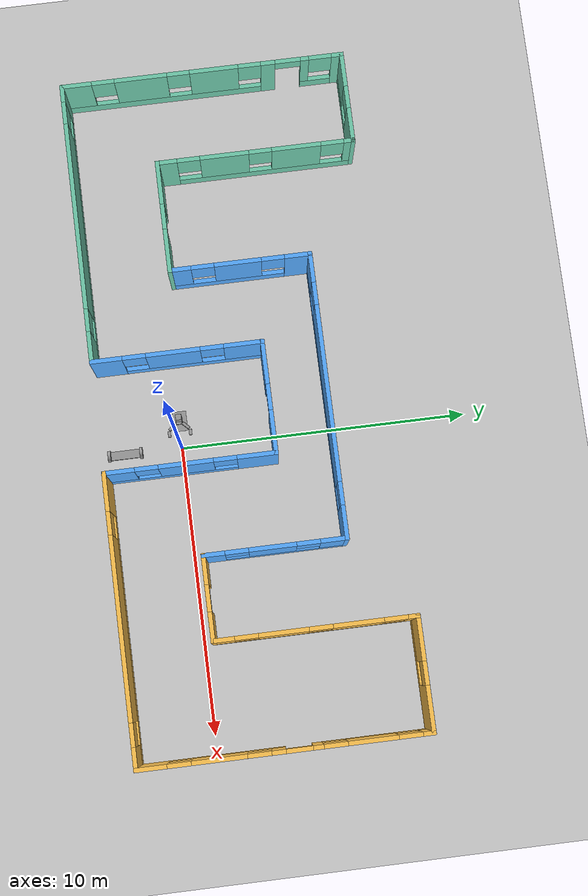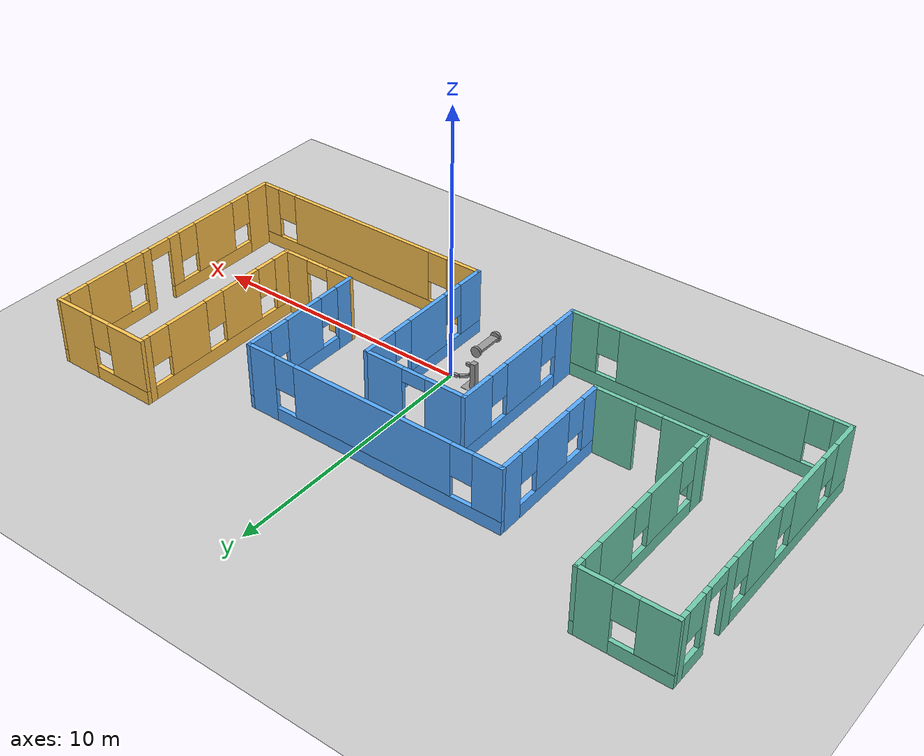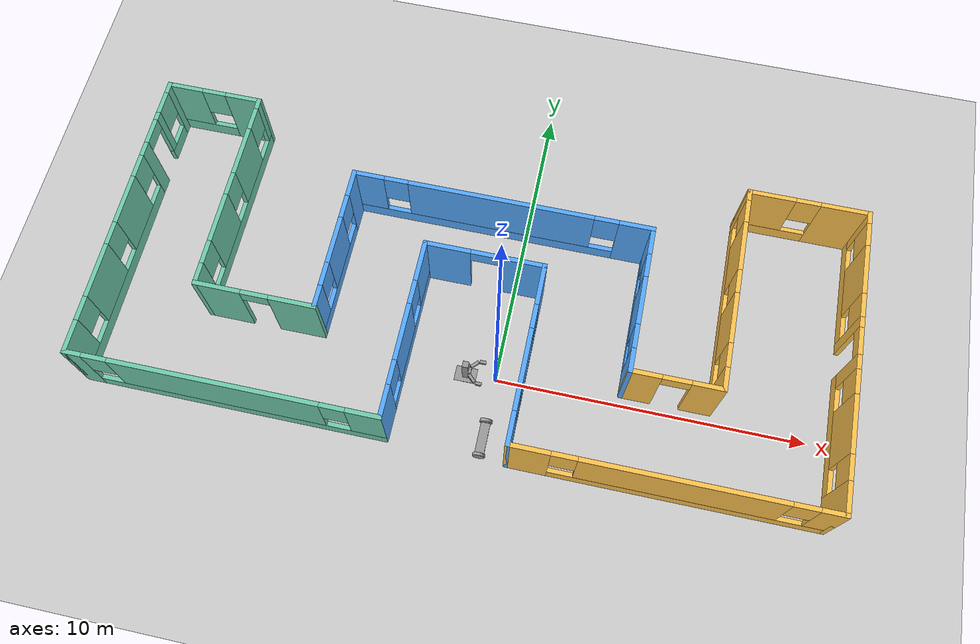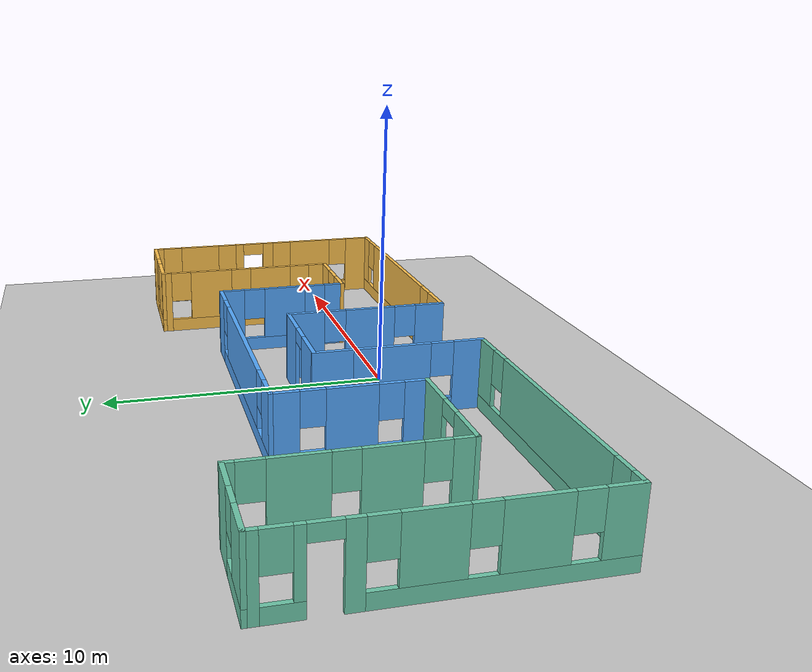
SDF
<sdf version="1.7">
 <world name="world2">
  <plugin name="welcome" filename="libwelcome.so"/>
  <light name="sun" type="directional">
   <pose>0 0 10 0 -0 0</pose>
   <diffuse>0.8 0.8 0.8 1</diffuse>
   <specular>0.2 0.2 0.2 1</specular>
   <attenuation>
    <range>1000</range>
    <constant>0.9</constant>
    <linear>0.01</linear>
    <quadratic>0.001</quadratic>
   </attenuation>
   <direction>-0.5 0.1 -0.9</direction>
   <spot><inner_angle>0</inner_angle><outer_angle>0</outer_angle><falloff>0</falloff></spot>
  </light>
  <model name="ground_plane">
   <static>1</static>
   <link name="link">
    <collision name="collision">
     <geometry><plane><normal>0 0 1</normal><size>100 100</size></plane></geometry>
     <surface><friction><ode><mu>100</mu><mu2>50</mu2></ode></friction></surface>
    </collision>
    <visual name="visual">
     <cast_shadows>0</cast_shadows>
     <geometry><plane><normal>0 0 1</normal><size>100 100</size></plane></geometry>
     <material>
      <script><uri>file://media/materials/scripts/gazebo.material</uri><name>Gazebo/Grey</name></script>
     </material>
    </visual>
   </link>
  </model>
  <gravity>0 0 -9.8</gravity>
  <magnetic_field>6e-06 2.3e-05 -4.2e-05</magnetic_field>
  <atmosphere type="adiabatic"/>
  <physics type="ode">
   <max_step_size>0.001</max_step_size>
   <real_time_factor>1</real_time_factor>
   <real_time_update_rate>1000</real_time_update_rate>
  </physics>
  <scene><ambient>0.4 0.4 0.4 1</ambient><background>0.7 0.7 0.7 1</background><shadows>1</shadows></scene>
  <spherical_coordinates>
   <surface_model>EARTH_WGS84</surface_model>
   <latitude_deg>0</latitude_deg>
   <longitude_deg>0</longitude_deg>
   <elevation>0</elevation>
   <heading_deg>0</heading_deg>
  </spherical_coordinates>
  <include><uri>model://gripper_base</uri><name>gripper</name><pose>-1 0 0.5 0 0 0</pose></include>
  <include><uri>model://hoverboard</uri><name>hoverboard0</name><pose>0 -2 0.2 0 0 0</pose></include>
  <include><uri>model://hoverboard</uri><name>hoverboard1</name><pose>0 -5 -0.4 0 0 0.6</pose></include>
  <include><uri>model://building1</uri><name>building1</name></include>
 </world>
</sdf>

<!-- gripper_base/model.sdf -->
<sdf version='1.7'>
  <model name='gripper_base'>
    <link name='riser'>
      <pose>0.02 0.02 0 -2e-06 -1.6e-05 -0.000932</pose>
      <inertial>
        <mass>10</mass>
        <inertia>
          <ixx>0.166667</ixx>
          <ixy>0</ixy>
          <ixz>0</ixz>
          <iyy>0.166667</iyy>
          <iyz>0</iyz>
          <izz>0.166667</izz>
        </inertia>
        <pose>0 0 0 0 -0 0</pose>
      </inertial>
      <self_collide>0</self_collide>
      <kinematic>0</kinematic>
      <enable_wind>0</enable_wind>
      <gravity>1</gravity>
      <visual name='visual'>
        <pose>0 0 0 0 -0 0</pose>
        <geometry>
          <box>
            <size>0.2 0.2 1</size>
          </box>
        </geometry>
        <material>
          <lighting>1</lighting>
          <script>
            <uri>file://media/materials/scripts/gazebo.material</uri>
            <name>Gazebo/Grey</name>
          </script>
          <ambient>0.3 0.3 0.3 1</ambient>
          <diffuse>0.7 0.7 0.7 1</diffuse>
          <specular>0.01 0.01 0.01 1</specular>
          <emissive>0 0 0 1</emissive>
          <shader type='vertex'>
            <normal_map>__default__</normal_map>
          </shader>
        </material>
        <transparency>0</transparency>
        <cast_shadows>1</cast_shadows>
      </visual>
      <collision name='collision'>
        <laser_retro>0</laser_retro>
        <max_contacts>10</max_contacts>
        <pose>0 0 0 0 -0 0</pose>
        <geometry>
          <box>
            <size>0.2 0.2 1</size>
          </box>
        </geometry>
        <surface>
          <friction>
            <ode>
              <mu>1</mu>
              <mu2>1</mu2>
              <fdir1>0 0 0</fdir1>
              <slip1>0</slip1>
              <slip2>0</slip2>
            </ode>
            <torsional>
              <coefficient>1</coefficient>
              <patch_radius>0</patch_radius>
              <surface_radius>0</surface_radius>
              <use_patch_radius>1</use_patch_radius>
              <ode>
                <slip>0</slip>
              </ode>
            </torsional>
          </friction>
          <bounce>
            <restitution_coefficient>0</restitution_coefficient>
            <threshold>1e+06</threshold>
          </bounce>
          <contact>
            <collide_without_contact>0</collide_without_contact>
            <collide_without_contact_bitmask>1</collide_without_contact_bitmask>
            <collide_bitmask>1</collide_bitmask>
            <ode>
              <soft_cfm>0</soft_cfm>
              <soft_erp>0.2</soft_erp>
              <kp>1e+13</kp>
              <kd>1</kd>
              <max_vel>0.01</max_vel>
              <min_depth>0</min_depth>
            </ode>
            <bullet>
              <split_impulse>1</split_impulse>
              <split_impulse_penetration_threshold>-0.01</split_impulse_penetration_threshold>
              <soft_cfm>0</soft_cfm>
              <soft_erp>0.2</soft_erp>
              <kp>1e+13</kp>
              <kd>1</kd>
            </bullet>
          </contact>
        </surface>
      </collision>
    </link>
    <link name='left_finger'>
      <pose>0.27277 0.243512 -0 0 0 -0.7854</pose>
      <inertial>
        <mass>0.1</mass>
        <inertia>
          <ixx>0.166667</ixx>
          <ixy>0</ixy>
          <ixz>0</ixz>
          <iyy>0.166667</iyy>
          <iyz>0</iyz>
          <izz>0.166667</izz>
        </inertia>
        <pose>0 0 0 0 -0 0</pose>
      </inertial>
      <self_collide>0</self_collide>
      <kinematic>0</kinematic>
      <enable_wind>0</enable_wind>
      <visual name='visual'>
        <pose>0 0 0 0 -0 0</pose>
        <geometry>
          <box>
            <size>0.1 0.3 0.1</size>
          </box>
        </geometry>
        <material>
          <lighting>1</lighting>
          <script>
            <uri>file://media/materials/scripts/gazebo.material</uri>
            <name>Gazebo/Grey</name>
          </script>
          <ambient>0.3 0.3 0.3 1</ambient>
          <diffuse>0.7 0.7 0.7 1</diffuse>
          <specular>0.01 0.01 0.01 1</specular>
          <emissive>0 0 0 1</emissive>
          <shader type='vertex'>
            <normal_map>__default__</normal_map>
          </shader>
        </material>
        <transparency>0</transparency>
        <cast_shadows>1</cast_shadows>
      </visual>
      <collision name='collision'>
        <laser_retro>0</laser_retro>
        <max_contacts>10</max_contacts>
        <pose>0 0 0 0 -0 0</pose>
        <geometry>
          <box>
            <size>0.1 0.3 0.1</size>
          </box>
        </geometry>
        <surface>
          <friction>
            <ode>
              <mu>1</mu>
              <mu2>1</mu2>
              <fdir1>0 0 0</fdir1>
              <slip1>0</slip1>
              <slip2>0</slip2>
            </ode>
            <torsional>
              <coefficient>1</coefficient>
              <patch_radius>0</patch_radius>
              <surface_radius>0</surface_radius>
              <use_patch_radius>1</use_patch_radius>
              <ode>
                <slip>0</slip>
              </ode>
            </torsional>
          </friction>
          <bounce>
            <restitution_coefficient>0</restitution_coefficient>
            <threshold>1e+06</threshold>
          </bounce>
          <contact>
            <collide_without_contact>0</collide_without_contact>
            <collide_without_contact_bitmask>1</collide_without_contact_bitmask>
            <collide_bitmask>1</collide_bitmask>
            <ode>
              <soft_cfm>0</soft_cfm>
              <soft_erp>0.2</soft_erp>
              <kp>1e+13</kp>
              <kd>1</kd>
              <max_vel>0.01</max_vel>
              <min_depth>0</min_depth>
            </ode>
            <bullet>
              <split_impulse>1</split_impulse>
              <split_impulse_penetration_threshold>-0.01</split_impulse_penetration_threshold>
              <soft_cfm>0</soft_cfm>
              <soft_erp>0.2</soft_erp>
              <kp>1e+13</kp>
              <kd>1</kd>
            </bullet>
          </contact>
        </surface>
      </collision>
    </link>
    <link name='left_fingertip'>
      <pose>0.516026 0.369208 0 0 0 -1.5707</pose>
      <inertial>
        <mass>0.1</mass>
        <inertia>
          <ixx>0.166667</ixx>
          <ixy>0</ixy>
          <ixz>0</ixz>
          <iyy>0.166667</iyy>
          <iyz>0</iyz>
          <izz>0.166667</izz>
        </inertia>
        <pose>0 0 0 0 -0 0</pose>
      </inertial>
      <self_collide>0</self_collide>
      <kinematic>0</kinematic>
      <enable_wind>0</enable_wind>
      <visual name='visual'>
        <pose>0 0 0 0 -0 0</pose>
        <geometry>
          <box>
            <size>0.1 0.2 0.1</size>
          </box>
        </geometry>
        <material>
          <lighting>1</lighting>
          <script>
            <uri>file://media/materials/scripts/gazebo.material</uri>
            <name>Gazebo/Grey</name>
          </script>
          <ambient>0.3 0.3 0.3 1</ambient>
          <diffuse>0.7 0.7 0.7 1</diffuse>
          <specular>0.01 0.01 0.01 1</specular>
          <emissive>0 0 0 1</emissive>
          <shader type='vertex'>
            <normal_map>__default__</normal_map>
          </shader>
        </material>
        <transparency>0</transparency>
        <cast_shadows>1</cast_shadows>
      </visual>
      <collision name='collision'>
        <laser_retro>0</laser_retro>
        <max_contacts>10</max_contacts>
        <pose>0 0 0 0 -0 0</pose>
        <geometry>
          <box>
            <size>0.1 0.2 0.1</size>
          </box>
        </geometry>
        <surface>
          <friction>
            <ode>
              <mu>1</mu>
              <mu2>1</mu2>
              <fdir1>0 0 0</fdir1>
              <slip1>0</slip1>
              <slip2>0</slip2>
            </ode>
            <torsional>
              <coefficient>1</coefficient>
              <patch_radius>0</patch_radius>
              <surface_radius>0</surface_radius>
              <use_patch_radius>1</use_patch_radius>
              <ode>
                <slip>0</slip>
              </ode>
            </torsional>
          </friction>
          <bounce>
            <restitution_coefficient>0</restitution_coefficient>
            <threshold>1e+06</threshold>
          </bounce>
          <contact>
            <collide_without_contact>0</collide_without_contact>
            <collide_without_contact_bitmask>1</collide_without_contact_bitmask>
            <collide_bitmask>1</collide_bitmask>
            <ode>
              <soft_cfm>0</soft_cfm>
              <soft_erp>0.2</soft_erp>
              <kp>1e+13</kp>
              <kd>1</kd>
              <max_vel>0.01</max_vel>
              <min_depth>0</min_depth>
            </ode>
            <bullet>
              <split_impulse>1</split_impulse>
              <split_impulse_penetration_threshold>-0.01</split_impulse_penetration_threshold>
              <soft_cfm>0</soft_cfm>
              <soft_erp>0.2</soft_erp>
              <kp>1e+13</kp>
              <kd>1</kd>
            </bullet>
          </contact>
        </surface>
      </collision>
    </link>
    <link name='base'>
      <inertial>
        <mass>19</mass>
        <inertia>
          <ixx>0.395992</ixx>
          <ixy>0</ixy>
          <ixz>0</ixz>
          <iyy>0.395992</iyy>
          <iyz>0</iyz>
          <izz>0.791667</izz>
        </inertia>
        <pose>0 0 0 0 -0 0</pose>
      </inertial>
      <pose>0.020008 0.019999 -0.493 -0 -0 -0.000932</pose>
      <gravity>1</gravity>
      <self_collide>0</self_collide>
      <kinematic>0</kinematic>
      <enable_wind>0</enable_wind>
      <visual name='visual'>
        <pose>0 0 0 0 -0 0</pose>
        <geometry>
          <box>
            <size>0.7 0.5 0.01</size>
          </box>
        </geometry>
        <material>
          <lighting>1</lighting>
          <script>
            <uri>file://media/materials/scripts/gazebo.material</uri>
            <name>Gazebo/Grey</name>
          </script>
          <shader type='pixel'>
            <normal_map>__default__</normal_map>
          </shader>
          <ambient>0.3 0.3 0.3 1</ambient>
          <diffuse>0.7 0.7 0.7 1</diffuse>
          <specular>0.01 0.01 0.01 1</specular>
          <emissive>0 0 0 1</emissive>
        </material>
        <transparency>0</transparency>
        <cast_shadows>1</cast_shadows>
      </visual>
      <collision name='collision'>
        <laser_retro>0</laser_retro>
        <max_contacts>10</max_contacts>
        <pose>0 0 0 0 -0 0</pose>
        <geometry>
          <box>
            <size>0.7 0.5 0.01</size>
          </box>
        </geometry>
        <surface>
          <friction>
            <ode>
              <mu>1</mu>
              <mu2>1</mu2>
              <fdir1>0 0 0</fdir1>
              <slip1>0</slip1>
              <slip2>0</slip2>
            </ode>
            <torsional>
              <coefficient>1</coefficient>
              <patch_radius>0</patch_radius>
              <surface_radius>0</surface_radius>
              <use_patch_radius>1</use_patch_radius>
              <ode>
                <slip>0</slip>
              </ode>
            </torsional>
          </friction>
          <bounce>
            <restitution_coefficient>0</restitution_coefficient>
            <threshold>1e+06</threshold>
          </bounce>
          <contact>
            <collide_without_contact>0</collide_without_contact>
            <collide_without_contact_bitmask>1</collide_without_contact_bitmask>
            <collide_bitmask>1</collide_bitmask>
            <ode>
              <soft_cfm>0</soft_cfm>
              <soft_erp>0.2</soft_erp>
              <kp>1e+13</kp>
              <kd>1</kd>
              <max_vel>0.01</max_vel>
              <min_depth>0</min_depth>
            </ode>
            <bullet>
              <split_impulse>1</split_impulse>
              <split_impulse_penetration_threshold>-0.01</split_impulse_penetration_threshold>
              <soft_cfm>0</soft_cfm>
              <soft_erp>0.2</soft_erp>
              <kp>1e+13</kp>
              <kd>1</kd>
            </bullet>
          </contact>
        </surface>
      </collision>
    </link>
    <link name='palm'>
      <pose>0.15 -0 -0 0 -0 0</pose>
      <inertial>
        <mass>0.5</mass>
        <inertia>
          <ixx>0.166667</ixx>
          <ixy>0</ixy>
          <ixz>0</ixz>
          <iyy>0.166667</iyy>
          <iyz>0</iyz>
          <izz>0.166667</izz>
        </inertia>
        <pose>0 0 0 0 -0 0</pose>
      </inertial>
      <self_collide>0</self_collide>
      <kinematic>0</kinematic>
      <enable_wind>0</enable_wind>
      <visual name='visual'>
        <pose>0 0 0 0 -0 0</pose>
        <geometry>
          <box>
            <size>0.1 0.2 0.1</size>
          </box>
        </geometry>
        <material>
          <lighting>1</lighting>
          <script>
            <uri>file://media/materials/scripts/gazebo.material</uri>
            <name>Gazebo/Grey</name>
          </script>
          <ambient>0.3 0.3 0.3 1</ambient>
          <diffuse>0.7 0.7 0.7 1</diffuse>
          <specular>0.01 0.01 0.01 1</specular>
          <emissive>0 0 0 1</emissive>
          <shader type='vertex'>
            <normal_map>__default__</normal_map>
          </shader>
        </material>
        <transparency>0</transparency>
        <cast_shadows>1</cast_shadows>
      </visual>
      <collision name='collision'>
        <laser_retro>0</laser_retro>
        <max_contacts>10</max_contacts>
        <pose>0 0 0 0 -0 0</pose>
        <geometry>
          <box>
            <size>0.1 0.2 0.1</size>
          </box>
        </geometry>
        <surface>
          <friction>
            <ode>
              <mu>1</mu>
              <mu2>1</mu2>
              <fdir1>0 0 0</fdir1>
              <slip1>0</slip1>
              <slip2>0</slip2>
            </ode>
            <torsional>
              <coefficient>1</coefficient>
              <patch_radius>0</patch_radius>
              <surface_radius>0</surface_radius>
              <use_patch_radius>1</use_patch_radius>
              <ode>
                <slip>0</slip>
              </ode>
            </torsional>
          </friction>
          <bounce>
            <restitution_coefficient>0</restitution_coefficient>
            <threshold>1e+06</threshold>
          </bounce>
          <contact>
            <collide_without_contact>0</collide_without_contact>
            <collide_without_contact_bitmask>1</collide_without_contact_bitmask>
            <collide_bitmask>1</collide_bitmask>
            <ode>
              <soft_cfm>0</soft_cfm>
              <soft_erp>0.2</soft_erp>
              <kp>1e+13</kp>
              <kd>1</kd>
              <max_vel>0.01</max_vel>
              <min_depth>0</min_depth>
            </ode>
            <bullet>
              <split_impulse>1</split_impulse>
              <split_impulse_penetration_threshold>-0.01</split_impulse_penetration_threshold>
              <soft_cfm>0</soft_cfm>
              <soft_erp>0.2</soft_erp>
              <kp>1e+13</kp>
              <kd>1</kd>
            </bullet>
          </contact>
        </surface>
      </collision>
    </link>
    <link name='right_finger'>
      <pose>0.27277 -0.243512 0 0 -0 0.7854</pose>
      <inertial>
        <mass>0.1</mass>
        <inertia>
          <ixx>0.166667</ixx>
          <ixy>0</ixy>
          <ixz>0</ixz>
          <iyy>0.166667</iyy>
          <iyz>0</iyz>
          <izz>0.166667</izz>
        </inertia>
        <pose>0 0 0 0 -0 0</pose>
      </inertial>
      <self_collide>0</self_collide>
      <kinematic>0</kinematic>
      <enable_wind>0</enable_wind>
      <visual name='visual'>
        <pose>0 0 0 0 -0 0</pose>
        <geometry>
          <box>
            <size>0.1 0.3 0.1</size>
          </box>
        </geometry>
        <material>
          <lighting>1</lighting>
          <script>
            <uri>file://media/materials/scripts/gazebo.material</uri>
            <name>Gazebo/Grey</name>
          </script>
          <ambient>0.3 0.3 0.3 1</ambient>
          <diffuse>0.7 0.7 0.7 1</diffuse>
          <specular>0.01 0.01 0.01 1</specular>
          <emissive>0 0 0 1</emissive>
          <shader type='vertex'>
            <normal_map>__default__</normal_map>
          </shader>
        </material>
        <transparency>0</transparency>
        <cast_shadows>1</cast_shadows>
      </visual>
      <collision name='collision'>
        <laser_retro>0</laser_retro>
        <max_contacts>10</max_contacts>
        <pose>0 0 0 0 -0 0</pose>
        <geometry>
          <box>
            <size>0.1 0.3 0.1</size>
          </box>
        </geometry>
        <surface>
          <friction>
            <ode>
              <mu>1</mu>
              <mu2>1</mu2>
              <fdir1>0 0 0</fdir1>
              <slip1>0</slip1>
              <slip2>0</slip2>
            </ode>
            <torsional>
              <coefficient>1</coefficient>
              <patch_radius>0</patch_radius>
              <surface_radius>0</surface_radius>
              <use_patch_radius>1</use_patch_radius>
              <ode>
                <slip>0</slip>
              </ode>
            </torsional>
          </friction>
          <bounce>
            <restitution_coefficient>0</restitution_coefficient>
            <threshold>1e+06</threshold>
          </bounce>
          <contact>
            <collide_without_contact>0</collide_without_contact>
            <collide_without_contact_bitmask>1</collide_without_contact_bitmask>
            <collide_bitmask>1</collide_bitmask>
            <ode>
              <soft_cfm>0</soft_cfm>
              <soft_erp>0.2</soft_erp>
              <kp>1e+13</kp>
              <kd>1</kd>
              <max_vel>0.01</max_vel>
              <min_depth>0</min_depth>
            </ode>
            <bullet>
              <split_impulse>1</split_impulse>
              <split_impulse_penetration_threshold>-0.01</split_impulse_penetration_threshold>
              <soft_cfm>0</soft_cfm>
              <soft_erp>0.2</soft_erp>
              <kp>1e+13</kp>
              <kd>1</kd>
            </bullet>
          </contact>
        </surface>
      </collision>
    </link>
    <link name='right_fingertip'>
      <pose>0.516026 -0.369208 -0 0 -0 1.5707</pose>
      <inertial>
        <mass>0.1</mass>
        <inertia>
          <ixx>0.166667</ixx>
          <ixy>0</ixy>
          <ixz>0</ixz>
          <iyy>0.166667</iyy>
          <iyz>0</iyz>
          <izz>0.166667</izz>
        </inertia>
        <pose>0 0 0 0 -0 0</pose>
      </inertial>
      <self_collide>0</self_collide>
      <kinematic>0</kinematic>
      <enable_wind>0</enable_wind>
      <visual name='visual'>
        <pose>0 0 0 0 -0 0</pose>
        <geometry>
          <box>
            <size>0.1 0.2 0.1</size>
          </box>
        </geometry>
        <material>
          <lighting>1</lighting>
          <script>
            <uri>file://media/materials/scripts/gazebo.material</uri>
            <name>Gazebo/Grey</name>
          </script>
          <ambient>0.3 0.3 0.3 1</ambient>
          <diffuse>0.7 0.7 0.7 1</diffuse>
          <specular>0.01 0.01 0.01 1</specular>
          <emissive>0 0 0 1</emissive>
          <shader type='vertex'>
            <normal_map>__default__</normal_map>
          </shader>
        </material>
        <transparency>0</transparency>
        <cast_shadows>1</cast_shadows>
      </visual>
      <collision name='collision'>
        <laser_retro>0</laser_retro>
        <max_contacts>10</max_contacts>
        <pose>0 0 0 0 -0 0</pose>
        <geometry>
          <box>
            <size>0.1 0.2 0.1</size>
          </box>
        </geometry>
        <surface>
          <friction>
            <ode>
              <mu>1</mu>
              <mu2>1</mu2>
              <fdir1>0 0 0</fdir1>
              <slip1>0</slip1>
              <slip2>0</slip2>
            </ode>
            <torsional>
              <coefficient>1</coefficient>
              <patch_radius>0</patch_radius>
              <surface_radius>0</surface_radius>
              <use_patch_radius>1</use_patch_radius>
              <ode>
                <slip>0</slip>
              </ode>
            </torsional>
          </friction>
          <bounce>
            <restitution_coefficient>0</restitution_coefficient>
            <threshold>1e+06</threshold>
          </bounce>
          <contact>
            <collide_without_contact>0</collide_without_contact>
            <collide_without_contact_bitmask>1</collide_without_contact_bitmask>
            <collide_bitmask>1</collide_bitmask>
            <ode>
              <soft_cfm>0</soft_cfm>
              <soft_erp>0.2</soft_erp>
              <kp>1e+13</kp>
              <kd>1</kd>
              <max_vel>0.01</max_vel>
              <min_depth>0</min_depth>
            </ode>
            <bullet>
              <split_impulse>1</split_impulse>
              <split_impulse_penetration_threshold>-0.01</split_impulse_penetration_threshold>
              <soft_cfm>0</soft_cfm>
              <soft_erp>0.2</soft_erp>
              <kp>1e+13</kp>
              <kd>1</kd>
            </bullet>
          </contact>
        </surface>
      </collision>
    </link>
    <joint name='left_finger_joint' type='revolute'>
      <parent>palm</parent>
      <child>left_finger</child>
      <pose>0.05 -0.15 0 0 -0 0</pose>
      <axis>
        <xyz>0 0 -1</xyz>
        <limit>
          <lower>-0.4</lower>
          <upper>0.4</upper>
          <effort>-1</effort>
          <velocity>-1</velocity>
        </limit>
        <dynamics>
          <spring_reference>0</spring_reference>
          <spring_stiffness>0</spring_stiffness>
          <damping>0</damping>
          <friction>0</friction>
        </dynamics>
      </axis>
      <physics>
        <ode>
          <limit>
            <cfm>0</cfm>
            <erp>0.2</erp>
          </limit>
          <suspension>
            <cfm>0</cfm>
            <erp>0.2</erp>
          </suspension>
        </ode>
      </physics>
    </joint>
    <joint name='left_tip_joint' type='revolute'>
      <parent>left_finger</parent>
      <child>left_fingertip</child>
      <pose>0.05 -0.1 0 0 -0 0</pose>
      <axis>
        <xyz>0 0 -1</xyz>
        <limit>
          <lower>-0.4</lower>
          <upper>0.4</upper>
          <effort>-1</effort>
          <velocity>-1</velocity>
        </limit>
        <dynamics>
          <spring_reference>0</spring_reference>
          <spring_stiffness>0</spring_stiffness>
          <damping>0</damping>
          <friction>0</friction>
        </dynamics>
      </axis>
      <physics>
        <ode>
          <limit>
            <cfm>0</cfm>
            <erp>0.2</erp>
          </limit>
          <suspension>
            <cfm>0</cfm>
            <erp>0.2</erp>
          </suspension>
        </ode>
      </physics>
    </joint>
    <joint name='base_JOINT_0' type='fixed'>
      <parent>base</parent>
      <child>riser</child>
      <pose>0 0 0 0 -0 0</pose>
      <physics>
        <ode>
          <limit>
            <cfm>0</cfm>
            <erp>0.2</erp>
          </limit>
          <suspension>
            <cfm>0</cfm>
            <erp>0.2</erp>
          </suspension>
        </ode>
      </physics>
    </joint>
    <joint name='right_finger_joint' type='revolute'>
      <parent>palm</parent>
      <child>right_finger</child>
      <pose>0.05 0.15 0 0 -0 0</pose>
      <axis>
        <xyz>0 0 1</xyz>
        <limit>
          <lower>-0.4</lower>
          <upper>0.4</upper>
          <effort>-1</effort>
          <velocity>-1</velocity>
        </limit>
        <dynamics>
          <spring_reference>0</spring_reference>
          <spring_stiffness>0</spring_stiffness>
          <damping>0</damping>
          <friction>0</friction>
        </dynamics>
      </axis>
      <physics>
        <ode>
          <limit>
            <cfm>0</cfm>
            <erp>0.2</erp>
          </limit>
          <suspension>
            <cfm>0</cfm>
            <erp>0.2</erp>
          </suspension>
        </ode>
      </physics>
    </joint>
    <joint name='right_tip_joint' type='revolute'>
      <parent>right_finger</parent>
      <child>right_fingertip</child>
      <pose>0.05 0.1 0 0 -0 0</pose>
      <axis>
        <xyz>0 0 1</xyz>
        <limit>
          <lower>-0.4</lower>
          <upper>0.4</upper>
          <effort>-1</effort>
          <velocity>-1</velocity>
        </limit>
        <dynamics>
          <spring_reference>0</spring_reference>
          <spring_stiffness>0</spring_stiffness>
          <damping>0</damping>
          <friction>0</friction>
        </dynamics>
      </axis>
      <physics>
        <ode>
          <limit>
            <cfm>0</cfm>
            <erp>0.2</erp>
          </limit>
          <suspension>
            <cfm>0</cfm>
            <erp>0.2</erp>
          </suspension>
        </ode>
      </physics>
    </joint>
    <joint name='riser_joint' type='prismatic'>
      <parent>riser</parent>
      <child>palm</child>
      <pose>0 0 0 0 -0 0</pose>
      <axis>
        <xyz>0 0 1</xyz>
        <limit>
          <lower>-0.4</lower>
          <upper>0.4</upper>
          <effort>-1</effort>
          <velocity>-1</velocity>
        </limit>
        <dynamics>
          <spring_reference>0</spring_reference>
          <spring_stiffness>0</spring_stiffness>
          <damping>0</damping>
          <friction>0</friction>
        </dynamics>
      </axis>
      <physics>
        <ode>
          <limit>
            <cfm>0</cfm>
            <erp>0.2</erp>
          </limit>
          <suspension>
            <cfm>0</cfm>
            <erp>0.2</erp>
          </suspension>
        </ode>
      </physics>
    </joint>
    <static>0</static>
    <allow_auto_disable>1</allow_auto_disable>
    <plugin name='gripper' filename='libgripper.so'>
      <riser_position>0</riser_position>
      <finger_position>0</finger_position>
      <tip_position>0</tip_position>
    </plugin>
  </model>
</sdf>

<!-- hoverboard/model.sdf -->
<sdf version='1.6'>
  <model name='hoverboard'>
    <link name='chassis'>
      <pose frame=''>0 0 0 0 -0 0</pose>
      <inertial>
        <mass>1</mass>
        <inertia>
          <ixx>0.166667</ixx>
          <ixy>0</ixy>
          <ixz>0</ixz>
          <iyy>0.166667</iyy>
          <iyz>0</iyz>
          <izz>0.166667</izz>
        </inertia>
        <pose frame=''>0 0 0 0 -0 0</pose>
      </inertial>
      <self_collide>0</self_collide>
      <kinematic>0</kinematic>
      <visual name='visual'>
        <pose frame=''>0 0 0 0 -0 0</pose>
        <geometry>
          <box>
            <size>0.3 1 0.1</size>
          </box>
        </geometry>
        <material>
          <lighting>1</lighting>
          <script>
            <uri>file://media/materials/scripts/gazebo.material</uri>
            <name>Gazebo/Grey</name>
          </script>
          <ambient>0.3 0.3 0.3 1</ambient>
          <diffuse>0.7 0.7 0.7 1</diffuse>
          <specular>0.01 0.01 0.01 1</specular>
          <emissive>0 0 0 1</emissive>
          <shader type='vertex'>
            <normal_map>__default__</normal_map>
          </shader>
        </material>
        <transparency>0</transparency>
        <cast_shadows>1</cast_shadows>
      </visual>
      <collision name='collision'>
        <laser_retro>0</laser_retro>
        <max_contacts>10</max_contacts>
        <pose frame=''>0 0 0 0 -0 0</pose>
        <geometry>
          <box>
            <size>0.3 1 0.1</size>
          </box>
        </geometry>
        <surface>
          <friction>
            <ode>
              <mu>1</mu>
              <mu2>1</mu2>
              <fdir1>0 0 0</fdir1>
              <slip1>0</slip1>
              <slip2>0</slip2>
            </ode>
            <torsional>
              <coefficient>1</coefficient>
              <patch_radius>0</patch_radius>
              <surface_radius>0</surface_radius>
              <use_patch_radius>1</use_patch_radius>
              <ode>
                <slip>0</slip>
              </ode>
            </torsional>
          </friction>
          <bounce>
            <restitution_coefficient>0</restitution_coefficient>
            <threshold>1e+06</threshold>
          </bounce>
          <contact>
            <collide_without_contact>0</collide_without_contact>
            <collide_without_contact_bitmask>1</collide_without_contact_bitmask>
            <collide_bitmask>1</collide_bitmask>
            <ode>
              <soft_cfm>0</soft_cfm>
              <soft_erp>0.2</soft_erp>
              <kp>1e+13</kp>
              <kd>1</kd>
              <max_vel>0.01</max_vel>
              <min_depth>0</min_depth>
            </ode>
            <bullet>
              <split_impulse>1</split_impulse>
              <split_impulse_penetration_threshold>-0.01</split_impulse_penetration_threshold>
              <soft_cfm>0</soft_cfm>
              <soft_erp>0.2</soft_erp>
              <kp>1e+13</kp>
              <kd>1</kd>
            </bullet>
          </contact>
        </surface>
      </collision>
    </link>
    <link name='left_wheel'>
      <pose frame=''>0 0.56 0 1.5707 -0 0</pose>
      <inertial>
        <mass>1</mass>
        <inertia>
          <ixx>0.145833</ixx>
          <ixy>0</ixy>
          <ixz>0</ixz>
          <iyy>0.145833</iyy>
          <iyz>0</iyz>
          <izz>0.125</izz>
        </inertia>
        <pose frame=''>0 0 0 0 -0 0</pose>
      </inertial>
      <self_collide>0</self_collide>
      <kinematic>0</kinematic>
      <visual name='visual'>
        <pose frame=''>0 0 0 0 -0 0</pose>
        <geometry>
          <cylinder>
            <radius>0.2</radius>
            <length>0.1</length>
          </cylinder>
        </geometry>
        <material>
          <lighting>1</lighting>
          <script>
            <uri>file://media/materials/scripts/gazebo.material</uri>
            <name>Gazebo/Grey</name>
          </script>
          <ambient>0.3 0.3 0.3 1</ambient>
          <diffuse>0.7 0.7 0.7 1</diffuse>
          <specular>0.01 0.01 0.01 1</specular>
          <emissive>0 0 0 1</emissive>
          <shader type='vertex'>
            <normal_map>__default__</normal_map>
          </shader>
        </material>
        <transparency>0</transparency>
        <cast_shadows>1</cast_shadows>
      </visual>
      <collision name='collision'>
        <laser_retro>0</laser_retro>
        <max_contacts>10</max_contacts>
        <pose frame=''>0 0 0 0 -0 0</pose>
        <geometry>
          <cylinder>
            <radius>0.2</radius>
            <length>0.1</length>
          </cylinder>
        </geometry>
        <surface>
          <friction>
            <ode>
              <mu>1</mu>
              <mu2>1</mu2>
              <fdir1>0 0 0</fdir1>
              <slip1>0</slip1>
              <slip2>0</slip2>
            </ode>
            <torsional>
              <coefficient>1</coefficient>
              <patch_radius>0</patch_radius>
              <surface_radius>0</surface_radius>
              <use_patch_radius>1</use_patch_radius>
              <ode>
                <slip>0</slip>
              </ode>
            </torsional>
          </friction>
          <bounce>
            <restitution_coefficient>0</restitution_coefficient>
            <threshold>1e+06</threshold>
          </bounce>
          <contact>
            <collide_without_contact>0</collide_without_contact>
            <collide_without_contact_bitmask>1</collide_without_contact_bitmask>
            <collide_bitmask>1</collide_bitmask>
            <ode>
              <soft_cfm>0</soft_cfm>
              <soft_erp>0.2</soft_erp>
              <kp>1e+13</kp>
              <kd>1</kd>
              <max_vel>0.01</max_vel>
              <min_depth>0</min_depth>
            </ode>
            <bullet>
              <split_impulse>1</split_impulse>
              <split_impulse_penetration_threshold>-0.01</split_impulse_penetration_threshold>
              <soft_cfm>0</soft_cfm>
              <soft_erp>0.2</soft_erp>
              <kp>1e+13</kp>
              <kd>1</kd>
            </bullet>
          </contact>
        </surface>
      </collision>
    </link>
    <link name='right_wheel'>
      <pose frame=''>0 -0.56 0 1.5707 -0 0</pose>
      <inertial>
        <mass>1</mass>
        <inertia>
          <ixx>0.145833</ixx>
          <ixy>0</ixy>
          <ixz>0</ixz>
          <iyy>0.145833</iyy>
          <iyz>0</iyz>
          <izz>0.125</izz>
        </inertia>
        <pose frame=''>0 0 0 0 -0 0</pose>
      </inertial>
      <self_collide>0</self_collide>
      <kinematic>0</kinematic>
      <visual name='visual'>
        <pose frame=''>0 0 0 0 -0 0</pose>
        <geometry>
          <cylinder>
            <radius>0.2</radius>
            <length>0.1</length>
          </cylinder>
        </geometry>
        <material>
          <lighting>1</lighting>
          <script>
            <uri>file://media/materials/scripts/gazebo.material</uri>
            <name>Gazebo/Grey</name>
          </script>
          <ambient>0.3 0.3 0.3 1</ambient>
          <diffuse>0.7 0.7 0.7 1</diffuse>
          <specular>0.01 0.01 0.01 1</specular>
          <emissive>0 0 0 1</emissive>
          <shader type='vertex'>
            <normal_map>__default__</normal_map>
          </shader>
        </material>
        <transparency>0</transparency>
        <cast_shadows>1</cast_shadows>
      </visual>
      <collision name='collision'>
        <laser_retro>0</laser_retro>
        <max_contacts>10</max_contacts>
        <pose frame=''>0 0 0 0 -0 0</pose>
        <geometry>
          <cylinder>
            <radius>0.2</radius>
            <length>0.1</length>
          </cylinder>
        </geometry>
        <surface>
          <friction>
            <ode>
              <mu>1</mu>
              <mu2>1</mu2>
              <fdir1>0 0 0</fdir1>
              <slip1>0</slip1>
              <slip2>0</slip2>
            </ode>
            <torsional>
              <coefficient>1</coefficient>
              <patch_radius>0</patch_radius>
              <surface_radius>0</surface_radius>
              <use_patch_radius>1</use_patch_radius>
              <ode>
                <slip>0</slip>
              </ode>
            </torsional>
          </friction>
          <bounce>
            <restitution_coefficient>0</restitution_coefficient>
            <threshold>1e+06</threshold>
          </bounce>
          <contact>
            <collide_without_contact>0</collide_without_contact>
            <collide_without_contact_bitmask>1</collide_without_contact_bitmask>
            <collide_bitmask>1</collide_bitmask>
            <ode>
              <soft_cfm>0</soft_cfm>
              <soft_erp>0.2</soft_erp>
              <kp>1e+13</kp>
              <kd>1</kd>
              <max_vel>0.01</max_vel>
              <min_depth>0</min_depth>
            </ode>
            <bullet>
              <split_impulse>1</split_impulse>
              <split_impulse_penetration_threshold>-0.01</split_impulse_penetration_threshold>
              <soft_cfm>0</soft_cfm>
              <soft_erp>0.2</soft_erp>
              <kp>1e+13</kp>
              <kd>1</kd>
            </bullet>
          </contact>
        </surface>
      </collision>
    </link>
    <joint name='left_wheel_joint' type='revolute'>
      <parent>chassis</parent>
      <child>left_wheel</child>
      <pose frame=''>0 0 0 0 -0 0</pose>
      <axis>
        <xyz>0 1 0</xyz>
        <use_parent_model_frame>1</use_parent_model_frame>
        <limit>
          <lower>-1.79769e+308</lower>
          <upper>1.79769e+308</upper>
          <effort>-1</effort>
          <velocity>-1</velocity>
        </limit>
        <dynamics>
          <spring_reference>0</spring_reference>
          <spring_stiffness>0</spring_stiffness>
          <damping>0</damping>
          <friction>0</friction>
        </dynamics>
      </axis>
      <physics>
        <ode>
          <limit>
            <cfm>0</cfm>
            <erp>0.2</erp>
          </limit>
          <suspension>
            <cfm>0</cfm>
            <erp>0.2</erp>
          </suspension>
        </ode>
      </physics>
    </joint>
    <joint name='right_wheel_joint' type='revolute'>
      <parent>chassis</parent>
      <child>right_wheel</child>
      <pose frame=''>0 0 0 0 -0 0</pose>
      <axis>
        <xyz>0 1 0</xyz>
        <use_parent_model_frame>1</use_parent_model_frame>
        <limit>
          <lower>-1.79769e+308</lower>
          <upper>1.79769e+308</upper>
          <effort>-1</effort>
          <velocity>-1</velocity>
        </limit>
        <dynamics>
          <spring_reference>0</spring_reference>
          <spring_stiffness>0</spring_stiffness>
          <damping>0</damping>
          <friction>0</friction>
        </dynamics>
      </axis>
      <physics>
        <ode>
          <limit>
            <cfm>0</cfm>
            <erp>0.2</erp>
          </limit>
          <suspension>
            <cfm>0</cfm>
            <erp>0.2</erp>
          </suspension>
        </ode>
      </physics>
    </joint>
    <static>0</static>
    <allow_auto_disable>1</allow_auto_disable>
    <plugin name='hoverboard' filename='libhoverboard.so'>
    <lin_velocity>0</lin_velocity>
    <ang_velocity>0</ang_velocity>
    </plugin>
  </model>
</sdf>

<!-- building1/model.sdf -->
<sdf version='1.6'>
  <model name='building1'>
    <pose frame=''>-1.05133 2.29231 0 0 -0 0</pose>
    <link name='Wall_10'>
      <pose frame=''>7.925 1.5 0 0 0 -1.5708</pose>
      <visual name='Wall_10_Visual_0'>
        <pose frame=''>-3.29894 0 1.25 0 -0 0</pose>
        <geometry>
          <box>
            <size>0.40213 0.15 2.5</size>
          </box>
        </geometry>
        <material>
          <script>
            <uri>file://media/materials/scripts/gazebo.material</uri>
            <name>Gazebo/Grey</name>
          </script>
          <ambient>1 0.764706 0.305882 1</ambient>
        </material>
        <meta>
          <layer>0</layer>
        </meta>
      </visual>
      <collision name='Wall_10_Collision_0'>
        <geometry>
          <box>
            <size>0.40213 0.15 2.5</size>
          </box>
        </geometry>
        <pose frame=''>-3.29894 0 1.25 0 -0 0</pose>
      </collision>
      <visual name='Wall_10_Visual_1'>
        <pose frame=''>0.201065 0 0.25 0 -0 0</pose>
        <geometry>
          <box>
            <size>6.59787 0.15 0.5</size>
          </box>
        </geometry>
        <material>
          <script>
            <uri>file://media/materials/scripts/gazebo.material</uri>
            <name>Gazebo/Grey</name>
          </script>
          <ambient>1 0.764706 0.305882 1</ambient>
        </material>
        <meta>
          <layer>0</layer>
        </meta>
      </visual>
      <collision name='Wall_10_Collision_1'>
        <geometry>
          <box>
            <size>6.59787 0.15 0.5</size>
          </box>
        </geometry>
        <pose frame=''>0.201065 0 0.25 0 -0 0</pose>
      </collision>
      <visual name='Wall_10_Visual_2'>
        <pose frame=''>-1.44224 0 1.5 0 -0 0</pose>
        <geometry>
          <box>
            <size>1.71126 0.15 2</size>
          </box>
        </geometry>
        <material>
          <script>
            <uri>file://media/materials/scripts/gazebo.material</uri>
            <name>Gazebo/Grey</name>
          </script>
          <ambient>1 0.764706 0.305882 1</ambient>
        </material>
        <meta>
          <layer>0</layer>
        </meta>
      </visual>
      <collision name='Wall_10_Collision_2'>
        <geometry>
          <box>
            <size>1.71126 0.15 2</size>
          </box>
        </geometry>
        <pose frame=''>-1.44224 0 1.5 0 -0 0</pose>
      </collision>
      <visual name='Wall_10_Visual_3'>
        <pose frame=''>1.0615 0 1.5 0 -0 0</pose>
        <geometry>
          <box>
            <size>1.69622 0.15 2</size>
          </box>
        </geometry>
        <material>
          <script>
            <uri>file://media/materials/scripts/gazebo.material</uri>
            <name>Gazebo/Grey</name>
          </script>
          <ambient>1 0.764706 0.305882 1</ambient>
        </material>
        <meta>
          <layer>0</layer>
        </meta>
      </visual>
      <collision name='Wall_10_Collision_3'>
        <geometry>
          <box>
            <size>1.69622 0.15 2</size>
          </box>
        </geometry>
        <pose frame=''>1.0615 0 1.5 0 -0 0</pose>
      </collision>
      <visual name='Wall_10_Visual_4'>
        <pose frame=''>3.1048 0 1.5 0 -0 0</pose>
        <geometry>
          <box>
            <size>0.790389 0.15 2</size>
          </box>
        </geometry>
        <material>
          <script>
            <uri>file://media/materials/scripts/gazebo.material</uri>
            <name>Gazebo/Grey</name>
          </script>
          <ambient>1 0.764706 0.305882 1</ambient>
        </material>
        <meta>
          <layer>0</layer>
        </meta>
      </visual>
      <collision name='Wall_10_Collision_4'>
        <geometry>
          <box>
            <size>0.790389 0.15 2</size>
          </box>
        </geometry>
        <pose frame=''>3.1048 0 1.5 0 -0 0</pose>
      </collision>
      <visual name='Wall_10_Visual_5'>
        <pose frame=''>-2.69787 0 1.9 0 -0 0</pose>
        <geometry>
          <box>
            <size>0.8 0.15 1.2</size>
          </box>
        </geometry>
        <material>
          <script>
            <uri>file://media/materials/scripts/gazebo.material</uri>
            <name>Gazebo/Grey</name>
          </script>
          <ambient>1 0.764706 0.305882 1</ambient>
        </material>
        <meta>
          <layer>0</layer>
        </meta>
      </visual>
      <collision name='Wall_10_Collision_5'>
        <geometry>
          <box>
            <size>0.8 0.15 1.2</size>
          </box>
        </geometry>
        <pose frame=''>-2.69787 0 1.9 0 -0 0</pose>
      </collision>
      <visual name='Wall_10_Visual_6'>
        <pose frame=''>-0.186611 0 1.9 0 -0 0</pose>
        <geometry>
          <box>
            <size>0.8 0.15 1.2</size>
          </box>
        </geometry>
        <material>
          <script>
            <uri>file://media/materials/scripts/gazebo.material</uri>
            <name>Gazebo/Grey</name>
          </script>
          <ambient>1 0.764706 0.305882 1</ambient>
        </material>
        <meta>
          <layer>0</layer>
        </meta>
      </visual>
      <collision name='Wall_10_Collision_6'>
        <geometry>
          <box>
            <size>0.8 0.15 1.2</size>
          </box>
        </geometry>
        <pose frame=''>-0.186611 0 1.9 0 -0 0</pose>
      </collision>
      <visual name='Wall_10_Visual_7'>
        <pose frame=''>2.30961 0 1.9 0 -0 0</pose>
        <geometry>
          <box>
            <size>0.8 0.15 1.2</size>
          </box>
        </geometry>
        <material>
          <script>
            <uri>file://media/materials/scripts/gazebo.material</uri>
            <name>Gazebo/Grey</name>
          </script>
          <ambient>1 0.764706 0.305882 1</ambient>
        </material>
        <meta>
          <layer>0</layer>
        </meta>
      </visual>
      <collision name='Wall_10_Collision_7'>
        <geometry>
          <box>
            <size>0.8 0.15 1.2</size>
          </box>
        </geometry>
        <pose frame=''>2.30961 0 1.9 0 -0 0</pose>
      </collision>
    </link>
    <link name='Wall_11'>
      <pose frame=''>6.5 -1.925 0 0 -0 3.14159</pose>
      <visual name='Wall_11_Visual_0'>
        <pose frame=''>-0.975368 0 1.25 0 -0 0</pose>
        <geometry>
          <box>
            <size>1.04926 0.15 2.5</size>
          </box>
        </geometry>
        <material>
          <script>
            <uri>file://media/materials/scripts/gazebo.material</uri>
            <name>Gazebo/Grey</name>
          </script>
          <ambient>1 0.764706 0.305882 1</ambient>
        </material>
        <meta>
          <layer>0</layer>
        </meta>
      </visual>
      <collision name='Wall_11_Collision_0'>
        <geometry>
          <box>
            <size>1.04926 0.15 2.5</size>
          </box>
        </geometry>
        <pose frame=''>-0.975368 0 1.25 0 -0 0</pose>
      </collision>
      <visual name='Wall_11_Visual_1'>
        <pose frame=''>0.974632 0 1.25 0 -0 0</pose>
        <geometry>
          <box>
            <size>1.05073 0.15 2.5</size>
          </box>
        </geometry>
        <material>
          <script>
            <uri>file://media/materials/scripts/gazebo.material</uri>
            <name>Gazebo/Grey</name>
          </script>
          <ambient>1 0.764706 0.305882 1</ambient>
        </material>
        <meta>
          <layer>0</layer>
        </meta>
      </visual>
      <collision name='Wall_11_Collision_1'>
        <geometry>
          <box>
            <size>1.05073 0.15 2.5</size>
          </box>
        </geometry>
        <pose frame=''>0.974632 0 1.25 0 -0 0</pose>
      </collision>
      <visual name='Wall_11_Visual_2'>
        <pose frame=''>-0.000735 0 2.25 0 -0 0</pose>
        <geometry>
          <box>
            <size>0.9 0.15 0.5</size>
          </box>
        </geometry>
        <material>
          <script>
            <uri>file://media/materials/scripts/gazebo.material</uri>
            <name>Gazebo/Grey</name>
          </script>
          <ambient>1 0.764706 0.305882 1</ambient>
        </material>
        <meta>
          <layer>0</layer>
        </meta>
      </visual>
      <collision name='Wall_11_Collision_2'>
        <geometry>
          <box>
            <size>0.9 0.15 0.5</size>
          </box>
        </geometry>
        <pose frame=''>-0.000735 0 2.25 0 -0 0</pose>
      </collision>
    </link>
    <link name='Wall_12'>
      <pose frame=''>5.075 0.5 0 0 -0 1.5708</pose>
      <visual name='Wall_12_Visual_0'>
        <pose frame=''>-2.09729 0 1.25 0 -0 0</pose>
        <geometry>
          <box>
            <size>0.805427 0.15 2.5</size>
          </box>
        </geometry>
        <material>
          <script>
            <uri>file://media/materials/scripts/gazebo.material</uri>
            <name>Gazebo/Grey</name>
          </script>
          <ambient>0.333333 0.666667 1 1</ambient>
        </material>
        <meta>
          <layer>0</layer>
        </meta>
      </visual>
      <collision name='Wall_12_Collision_0'>
        <geometry>
          <box>
            <size>0.805427 0.15 2.5</size>
          </box>
        </geometry>
        <pose frame=''>-2.09729 0 1.25 0 -0 0</pose>
      </collision>
      <visual name='Wall_12_Visual_1'>
        <pose frame=''>0.402713 0 0.25 0 -0 0</pose>
        <geometry>
          <box>
            <size>4.19457 0.15 0.5</size>
          </box>
        </geometry>
        <material>
          <script>
            <uri>file://media/materials/scripts/gazebo.material</uri>
            <name>Gazebo/Grey</name>
          </script>
          <ambient>0.333333 0.666667 1 1</ambient>
        </material>
        <meta>
          <layer>0</layer>
        </meta>
      </visual>
      <collision name='Wall_12_Collision_1'>
        <geometry>
          <box>
            <size>4.19457 0.15 0.5</size>
          </box>
        </geometry>
        <pose frame=''>0.402713 0 0.25 0 -0 0</pose>
      </collision>
      <visual name='Wall_12_Visual_2'>
        <pose frame=''>-0.084056 0 1.5 0 -0 0</pose>
        <geometry>
          <box>
            <size>1.62103 0.15 2</size>
          </box>
        </geometry>
        <material>
          <script>
            <uri>file://media/materials/scripts/gazebo.material</uri>
            <name>Gazebo/Grey</name>
          </script>
          <ambient>0.333333 0.666667 1 1</ambient>
        </material>
        <meta>
          <layer>0</layer>
        </meta>
      </visual>
      <collision name='Wall_12_Collision_2'>
        <geometry>
          <box>
            <size>1.62103 0.15 2</size>
          </box>
        </geometry>
        <pose frame=''>-0.084056 0 1.5 0 -0 0</pose>
      </collision>
      <visual name='Wall_12_Visual_3'>
        <pose frame=''>2.01323 0 1.5 0 -0 0</pose>
        <geometry>
          <box>
            <size>0.973539 0.15 2</size>
          </box>
        </geometry>
        <material>
          <script>
            <uri>file://media/materials/scripts/gazebo.material</uri>
            <name>Gazebo/Grey</name>
          </script>
          <ambient>0.333333 0.666667 1 1</ambient>
        </material>
        <meta>
          <layer>0</layer>
        </meta>
      </visual>
      <collision name='Wall_12_Collision_3'>
        <geometry>
          <box>
            <size>0.973539 0.15 2</size>
          </box>
        </geometry>
        <pose frame=''>2.01323 0 1.5 0 -0 0</pose>
      </collision>
      <visual name='Wall_12_Visual_4'>
        <pose frame=''>-1.29457 0 1.9 0 -0 0</pose>
        <geometry>
          <box>
            <size>0.8 0.15 1.2</size>
          </box>
        </geometry>
        <material>
          <script>
            <uri>file://media/materials/scripts/gazebo.material</uri>
            <name>Gazebo/Grey</name>
          </script>
          <ambient>0.333333 0.666667 1 1</ambient>
        </material>
        <meta>
          <layer>0</layer>
        </meta>
      </visual>
      <collision name='Wall_12_Collision_4'>
        <geometry>
          <box>
            <size>0.8 0.15 1.2</size>
          </box>
        </geometry>
        <pose frame=''>-1.29457 0 1.9 0 -0 0</pose>
      </collision>
      <visual name='Wall_12_Visual_5'>
        <pose frame=''>1.12646 0 1.9 0 -0 0</pose>
        <geometry>
          <box>
            <size>0.8 0.15 1.2</size>
          </box>
        </geometry>
        <material>
          <script>
            <uri>file://media/materials/scripts/gazebo.material</uri>
            <name>Gazebo/Grey</name>
          </script>
          <ambient>0.333333 0.666667 1 1</ambient>
        </material>
        <meta>
          <layer>0</layer>
        </meta>
      </visual>
      <collision name='Wall_12_Collision_5'>
        <geometry>
          <box>
            <size>0.8 0.15 1.2</size>
          </box>
        </geometry>
        <pose frame=''>1.12646 0 1.9 0 -0 0</pose>
      </collision>
    </link>
    <link name='Wall_13'>
      <pose frame=''>0.15 2.925 0 0 -0 3.14159</pose>
      <visual name='Wall_13_Visual_0'>
        <pose frame=''>-4.40921 0 1.25 0 -0 0</pose>
        <geometry>
          <box>
            <size>1.18157 0.15 2.5</size>
          </box>
        </geometry>
        <material>
          <script>
            <uri>file://media/materials/scripts/gazebo.material</uri>
            <name>Gazebo/Grey</name>
          </script>
          <ambient>0.333333 0.666667 1 1</ambient>
        </material>
        <meta>
          <layer>0</layer>
        </meta>
      </visual>
      <collision name='Wall_13_Collision_0'>
        <geometry>
          <box>
            <size>1.18157 0.15 2.5</size>
          </box>
        </geometry>
        <pose frame=''>-4.40921 0 1.25 0 -0 0</pose>
      </collision>
      <visual name='Wall_13_Visual_1'>
        <pose frame=''>0.590787 0 0.25 0 -0 0</pose>
        <geometry>
          <box>
            <size>8.81843 0.15 0.5</size>
          </box>
        </geometry>
        <material>
          <script>
            <uri>file://media/materials/scripts/gazebo.material</uri>
            <name>Gazebo/Grey</name>
          </script>
          <ambient>0.333333 0.666667 1 1</ambient>
        </material>
        <meta>
          <layer>0</layer>
        </meta>
      </visual>
      <collision name='Wall_13_Collision_1'>
        <geometry>
          <box>
            <size>8.81843 0.15 0.5</size>
          </box>
        </geometry>
        <pose frame=''>0.590787 0 0.25 0 -0 0</pose>
      </collision>
      <visual name='Wall_13_Visual_2'>
        <pose frame=''>0.047713 0 1.5 0 -0 0</pose>
        <geometry>
          <box>
            <size>6.13228 0.15 2</size>
          </box>
        </geometry>
        <material>
          <script>
            <uri>file://media/materials/scripts/gazebo.material</uri>
            <name>Gazebo/Grey</name>
          </script>
          <ambient>0.333333 0.666667 1 1</ambient>
        </material>
        <meta>
          <layer>0</layer>
        </meta>
      </visual>
      <collision name='Wall_13_Collision_2'>
        <geometry>
          <box>
            <size>6.13228 0.15 2</size>
          </box>
        </geometry>
        <pose frame=''>0.047713 0 1.5 0 -0 0</pose>
      </collision>
      <visual name='Wall_13_Visual_3'>
        <pose frame=''>4.45693 0 1.5 0 -0 0</pose>
        <geometry>
          <box>
            <size>1.08615 0.15 2</size>
          </box>
        </geometry>
        <material>
          <script>
            <uri>file://media/materials/scripts/gazebo.material</uri>
            <name>Gazebo/Grey</name>
          </script>
          <ambient>0.333333 0.666667 1 1</ambient>
        </material>
        <meta>
          <layer>0</layer>
        </meta>
      </visual>
      <collision name='Wall_13_Collision_3'>
        <geometry>
          <box>
            <size>1.08615 0.15 2</size>
          </box>
        </geometry>
        <pose frame=''>4.45693 0 1.5 0 -0 0</pose>
      </collision>
      <visual name='Wall_13_Visual_4'>
        <pose frame=''>-3.41843 0 1.9 0 -0 0</pose>
        <geometry>
          <box>
            <size>0.8 0.15 1.2</size>
          </box>
        </geometry>
        <material>
          <script>
            <uri>file://media/materials/scripts/gazebo.material</uri>
            <name>Gazebo/Grey</name>
          </script>
          <ambient>0.333333 0.666667 1 1</ambient>
        </material>
        <meta>
          <layer>0</layer>
        </meta>
      </visual>
      <collision name='Wall_13_Collision_4'>
        <geometry>
          <box>
            <size>0.8 0.15 1.2</size>
          </box>
        </geometry>
        <pose frame=''>-3.41843 0 1.9 0 -0 0</pose>
      </collision>
      <visual name='Wall_13_Visual_5'>
        <pose frame=''>3.51385 0 1.9 0 -0 0</pose>
        <geometry>
          <box>
            <size>0.8 0.15 1.2</size>
          </box>
        </geometry>
        <material>
          <script>
            <uri>file://media/materials/scripts/gazebo.material</uri>
            <name>Gazebo/Grey</name>
          </script>
          <ambient>0.333333 0.666667 1 1</ambient>
        </material>
        <meta>
          <layer>0</layer>
        </meta>
      </visual>
      <collision name='Wall_13_Collision_5'>
        <geometry>
          <box>
            <size>0.8 0.15 1.2</size>
          </box>
        </geometry>
        <pose frame=''>3.51385 0 1.9 0 -0 0</pose>
      </collision>
    </link>
    <link name='Wall_14'>
      <pose frame=''>-4.775 0.5 0 0 0 -1.5708</pose>
      <visual name='Wall_14_Visual_0'>
        <pose frame=''>-2.02075 0 1.25 0 -0 0</pose>
        <geometry>
          <box>
            <size>0.958501 0.15 2.5</size>
          </box>
        </geometry>
        <material>
          <script>
            <uri>file://media/materials/scripts/gazebo.material</uri>
            <name>Gazebo/Grey</name>
          </script>
          <ambient>0.333333 0.666667 1 1</ambient>
        </material>
        <meta>
          <layer>0</layer>
        </meta>
      </visual>
      <collision name='Wall_14_Collision_0'>
        <geometry>
          <box>
            <size>0.958501 0.15 2.5</size>
          </box>
        </geometry>
        <pose frame=''>-2.02075 0 1.25 0 -0 0</pose>
      </collision>
      <visual name='Wall_14_Visual_1'>
        <pose frame=''>0.479251 0 0.25 0 -0 0</pose>
        <geometry>
          <box>
            <size>4.0415 0.15 0.5</size>
          </box>
        </geometry>
        <material>
          <script>
            <uri>file://media/materials/scripts/gazebo.material</uri>
            <name>Gazebo/Grey</name>
          </script>
          <ambient>0.333333 0.666667 1 1</ambient>
        </material>
        <meta>
          <layer>0</layer>
        </meta>
      </visual>
      <collision name='Wall_14_Collision_1'>
        <geometry>
          <box>
            <size>4.0415 0.15 0.5</size>
          </box>
        </geometry>
        <pose frame=''>0.479251 0 0.25 0 -0 0</pose>
      </collision>
      <visual name='Wall_14_Visual_2'>
        <pose frame=''>0.076537 0 1.5 0 -0 0</pose>
        <geometry>
          <box>
            <size>1.63607 0.15 2</size>
          </box>
        </geometry>
        <material>
          <script>
            <uri>file://media/materials/scripts/gazebo.material</uri>
            <name>Gazebo/Grey</name>
          </script>
          <ambient>0.333333 0.666667 1 1</ambient>
        </material>
        <meta>
          <layer>0</layer>
        </meta>
      </visual>
      <collision name='Wall_14_Collision_2'>
        <geometry>
          <box>
            <size>1.63607 0.15 2</size>
          </box>
        </geometry>
        <pose frame=''>0.076537 0 1.5 0 -0 0</pose>
      </collision>
      <visual name='Wall_14_Visual_3'>
        <pose frame=''>2.09729 0 1.5 0 -0 0</pose>
        <geometry>
          <box>
            <size>0.805427 0.15 2</size>
          </box>
        </geometry>
        <material>
          <script>
            <uri>file://media/materials/scripts/gazebo.material</uri>
            <name>Gazebo/Grey</name>
          </script>
          <ambient>0.333333 0.666667 1 1</ambient>
        </material>
        <meta>
          <layer>0</layer>
        </meta>
      </visual>
      <collision name='Wall_14_Collision_3'>
        <geometry>
          <box>
            <size>0.805427 0.15 2</size>
          </box>
        </geometry>
        <pose frame=''>2.09729 0 1.5 0 -0 0</pose>
      </collision>
      <visual name='Wall_14_Visual_4'>
        <pose frame=''>-1.1415 0 1.9 0 -0 0</pose>
        <geometry>
          <box>
            <size>0.8 0.15 1.2</size>
          </box>
        </geometry>
        <material>
          <script>
            <uri>file://media/materials/scripts/gazebo.material</uri>
            <name>Gazebo/Grey</name>
          </script>
          <ambient>0.333333 0.666667 1 1</ambient>
        </material>
        <meta>
          <layer>0</layer>
        </meta>
      </visual>
      <collision name='Wall_14_Collision_4'>
        <geometry>
          <box>
            <size>0.8 0.15 1.2</size>
          </box>
        </geometry>
        <pose frame=''>-1.1415 0 1.9 0 -0 0</pose>
      </collision>
      <visual name='Wall_14_Visual_5'>
        <pose frame=''>1.29457 0 1.9 0 -0 0</pose>
        <geometry>
          <box>
            <size>0.8 0.15 1.2</size>
          </box>
        </geometry>
        <material>
          <script>
            <uri>file://media/materials/scripts/gazebo.material</uri>
            <name>Gazebo/Grey</name>
          </script>
          <ambient>0.333333 0.666667 1 1</ambient>
        </material>
        <meta>
          <layer>0</layer>
        </meta>
      </visual>
      <collision name='Wall_14_Collision_5'>
        <geometry>
          <box>
            <size>0.8 0.15 1.2</size>
          </box>
        </geometry>
        <pose frame=''>1.29457 0 1.9 0 -0 0</pose>
      </collision>
    </link>
    <link name='Wall_15'>
      <pose frame=''>-6.7 -1.925 0 0 -0 3.14159</pose>
      <visual name='Wall_15_Visual_0'>
        <pose frame=''>-1.22391 0 1.25 0 -0 0</pose>
        <geometry>
          <box>
            <size>1.55217 0.15 2.5</size>
          </box>
        </geometry>
        <material>
          <script>
            <uri>file://media/materials/scripts/gazebo.material</uri>
            <name>Gazebo/Grey</name>
          </script>
          <ambient>0.435294 0.796078 0.67451 1</ambient>
        </material>
        <meta>
          <layer>0</layer>
        </meta>
      </visual>
      <collision name='Wall_15_Collision_0'>
        <geometry>
          <box>
            <size>1.55217 0.15 2.5</size>
          </box>
        </geometry>
        <pose frame=''>-1.22391 0 1.25 0 -0 0</pose>
      </collision>
      <visual name='Wall_15_Visual_1'>
        <pose frame=''>1.22609 0 1.25 0 -0 0</pose>
        <geometry>
          <box>
            <size>1.54783 0.15 2.5</size>
          </box>
        </geometry>
        <material>
          <script>
            <uri>file://media/materials/scripts/gazebo.material</uri>
            <name>Gazebo/Grey</name>
          </script>
          <ambient>0.435294 0.796078 0.67451 1</ambient>
        </material>
        <meta>
          <layer>0</layer>
        </meta>
      </visual>
      <collision name='Wall_15_Collision_1'>
        <geometry>
          <box>
            <size>1.54783 0.15 2.5</size>
          </box>
        </geometry>
        <pose frame=''>1.22609 0 1.25 0 -0 0</pose>
      </collision>
      <visual name='Wall_15_Visual_2'>
        <pose frame=''>0.002173 0 2.25 0 -0 0</pose>
        <geometry>
          <box>
            <size>0.9 0.15 0.5</size>
          </box>
        </geometry>
        <material>
          <script>
            <uri>file://media/materials/scripts/gazebo.material</uri>
            <name>Gazebo/Grey</name>
          </script>
          <ambient>0.435294 0.796078 0.67451 1</ambient>
        </material>
        <meta>
          <layer>0</layer>
        </meta>
      </visual>
      <collision name='Wall_15_Collision_2'>
        <geometry>
          <box>
            <size>0.9 0.15 0.5</size>
          </box>
        </geometry>
        <pose frame=''>0.002173 0 2.25 0 -0 0</pose>
      </collision>
    </link>
    <link name='Wall_16'>
      <pose frame=''>-8.625 1.5 0 0 -0 1.5708</pose>
      <visual name='Wall_16_Visual_0'>
        <pose frame=''>-3.11984 0 1.25 0 -0 0</pose>
        <geometry>
          <box>
            <size>0.760314 0.15 2.5</size>
          </box>
        </geometry>
        <material>
          <script>
            <uri>file://media/materials/scripts/gazebo.material</uri>
            <name>Gazebo/Grey</name>
          </script>
          <ambient>0.435294 0.796078 0.67451 1</ambient>
        </material>
        <meta>
          <layer>0</layer>
        </meta>
      </visual>
      <collision name='Wall_16_Collision_0'>
        <geometry>
          <box>
            <size>0.760314 0.15 2.5</size>
          </box>
        </geometry>
        <pose frame=''>-3.11984 0 1.25 0 -0 0</pose>
      </collision>
      <visual name='Wall_16_Visual_1'>
        <pose frame=''>0.380157 0 0.25 0 -0 0</pose>
        <geometry>
          <box>
            <size>6.23969 0.15 0.5</size>
          </box>
        </geometry>
        <material>
          <script>
            <uri>file://media/materials/scripts/gazebo.material</uri>
            <name>Gazebo/Grey</name>
          </script>
          <ambient>0.435294 0.796078 0.67451 1</ambient>
        </material>
        <meta>
          <layer>0</layer>
        </meta>
      </visual>
      <collision name='Wall_16_Collision_1'>
        <geometry>
          <box>
            <size>6.23969 0.15 0.5</size>
          </box>
        </geometry>
        <pose frame=''>0.380157 0 0.25 0 -0 0</pose>
      </collision>
      <visual name='Wall_16_Visual_2'>
        <pose frame=''>-1.08406 0 1.5 0 -0 0</pose>
        <geometry>
          <box>
            <size>1.71126 0.15 2</size>
          </box>
        </geometry>
        <material>
          <script>
            <uri>file://media/materials/scripts/gazebo.material</uri>
            <name>Gazebo/Grey</name>
          </script>
          <ambient>0.435294 0.796078 0.67451 1</ambient>
        </material>
        <meta>
          <layer>0</layer>
        </meta>
      </visual>
      <collision name='Wall_16_Collision_2'>
        <geometry>
          <box>
            <size>1.71126 0.15 2</size>
          </box>
        </geometry>
        <pose frame=''>-1.08406 0 1.5 0 -0 0</pose>
      </collision>
      <visual name='Wall_16_Visual_3'>
        <pose frame=''>1.43472 0 1.5 0 -0 0</pose>
        <geometry>
          <box>
            <size>1.7263 0.15 2</size>
          </box>
        </geometry>
        <material>
          <script>
            <uri>file://media/materials/scripts/gazebo.material</uri>
            <name>Gazebo/Grey</name>
          </script>
          <ambient>0.435294 0.796078 0.67451 1</ambient>
        </material>
        <meta>
          <layer>0</layer>
        </meta>
      </visual>
      <collision name='Wall_16_Collision_3'>
        <geometry>
          <box>
            <size>1.7263 0.15 2</size>
          </box>
        </geometry>
        <pose frame=''>1.43472 0 1.5 0 -0 0</pose>
      </collision>
      <visual name='Wall_16_Visual_4'>
        <pose frame=''>3.29894 0 1.5 0 -0 0</pose>
        <geometry>
          <box>
            <size>0.40213 0.15 2</size>
          </box>
        </geometry>
        <material>
          <script>
            <uri>file://media/materials/scripts/gazebo.material</uri>
            <name>Gazebo/Grey</name>
          </script>
          <ambient>0.435294 0.796078 0.67451 1</ambient>
        </material>
        <meta>
          <layer>0</layer>
        </meta>
      </visual>
      <collision name='Wall_16_Collision_4'>
        <geometry>
          <box>
            <size>0.40213 0.15 2</size>
          </box>
        </geometry>
        <pose frame=''>3.29894 0 1.5 0 -0 0</pose>
      </collision>
      <visual name='Wall_16_Visual_5'>
        <pose frame=''>-2.33969 0 1.9 0 -0 0</pose>
        <geometry>
          <box>
            <size>0.8 0.15 1.2</size>
          </box>
        </geometry>
        <material>
          <script>
            <uri>file://media/materials/scripts/gazebo.material</uri>
            <name>Gazebo/Grey</name>
          </script>
          <ambient>0.435294 0.796078 0.67451 1</ambient>
        </material>
        <meta>
          <layer>0</layer>
        </meta>
      </visual>
      <collision name='Wall_16_Collision_5'>
        <geometry>
          <box>
            <size>0.8 0.15 1.2</size>
          </box>
        </geometry>
        <pose frame=''>-2.33969 0 1.9 0 -0 0</pose>
      </collision>
      <visual name='Wall_16_Visual_6'>
        <pose frame=''>0.171574 0 1.9 0 -0 0</pose>
        <geometry>
          <box>
            <size>0.8 0.15 1.2</size>
          </box>
        </geometry>
        <material>
          <script>
            <uri>file://media/materials/scripts/gazebo.material</uri>
            <name>Gazebo/Grey</name>
          </script>
          <ambient>0.435294 0.796078 0.67451 1</ambient>
        </material>
        <meta>
          <layer>0</layer>
        </meta>
      </visual>
      <collision name='Wall_16_Collision_6'>
        <geometry>
          <box>
            <size>0.8 0.15 1.2</size>
          </box>
        </geometry>
        <pose frame=''>0.171574 0 1.9 0 -0 0</pose>
      </collision>
      <visual name='Wall_16_Visual_7'>
        <pose frame=''>2.69787 0 1.9 0 -0 0</pose>
        <geometry>
          <box>
            <size>0.8 0.15 1.2</size>
          </box>
        </geometry>
        <material>
          <script>
            <uri>file://media/materials/scripts/gazebo.material</uri>
            <name>Gazebo/Grey</name>
          </script>
          <ambient>0.435294 0.796078 0.67451 1</ambient>
        </material>
        <meta>
          <layer>0</layer>
        </meta>
      </visual>
      <collision name='Wall_16_Collision_7'>
        <geometry>
          <box>
            <size>0.8 0.15 1.2</size>
          </box>
        </geometry>
        <pose frame=''>2.69787 0 1.9 0 -0 0</pose>
      </collision>
    </link>
    <link name='Wall_17'>
      <pose frame=''>-10.2 4.925 0 0 -0 3.14159</pose>
      <visual name='Wall_17_Visual_0'>
        <pose frame=''>-1.02361 0 1.25 0 -0 0</pose>
        <geometry>
          <box>
            <size>1.25279 0.15 2.5</size>
          </box>
        </geometry>
        <material>
          <script>
            <uri>file://media/materials/scripts/gazebo.material</uri>
            <name>Gazebo/Grey</name>
          </script>
          <ambient>0.435294 0.796078 0.67451 1</ambient>
        </material>
        <meta>
          <layer>0</layer>
        </meta>
      </visual>
      <collision name='Wall_17_Collision_0'>
        <geometry>
          <box>
            <size>1.25279 0.15 2.5</size>
          </box>
        </geometry>
        <pose frame=''>-1.02361 0 1.25 0 -0 0</pose>
      </collision>
      <visual name='Wall_17_Visual_1'>
        <pose frame=''>0.626392 0 0.25 0 -0 0</pose>
        <geometry>
          <box>
            <size>2.04722 0.15 0.5</size>
          </box>
        </geometry>
        <material>
          <script>
            <uri>file://media/materials/scripts/gazebo.material</uri>
            <name>Gazebo/Grey</name>
          </script>
          <ambient>0.435294 0.796078 0.67451 1</ambient>
        </material>
        <meta>
          <layer>0</layer>
        </meta>
      </visual>
      <collision name='Wall_17_Collision_1'>
        <geometry>
          <box>
            <size>2.04722 0.15 0.5</size>
          </box>
        </geometry>
        <pose frame=''>0.626392 0 0.25 0 -0 0</pose>
      </collision>
      <visual name='Wall_17_Visual_2'>
        <pose frame=''>1.02639 0 1.5 0 -0 0</pose>
        <geometry>
          <box>
            <size>1.24721 0.15 2</size>
          </box>
        </geometry>
        <material>
          <script>
            <uri>file://media/materials/scripts/gazebo.material</uri>
            <name>Gazebo/Grey</name>
          </script>
          <ambient>0.435294 0.796078 0.67451 1</ambient>
        </material>
        <meta>
          <layer>0</layer>
        </meta>
      </visual>
      <collision name='Wall_17_Collision_2'>
        <geometry>
          <box>
            <size>1.24721 0.15 2</size>
          </box>
        </geometry>
        <pose frame=''>1.02639 0 1.5 0 -0 0</pose>
      </collision>
      <visual name='Wall_17_Visual_3'>
        <pose frame=''>0.002785 0 1.9 0 -0 0</pose>
        <geometry>
          <box>
            <size>0.8 0.15 1.2</size>
          </box>
        </geometry>
        <material>
          <script>
            <uri>file://media/materials/scripts/gazebo.material</uri>
            <name>Gazebo/Grey</name>
          </script>
          <ambient>0.435294 0.796078 0.67451 1</ambient>
        </material>
        <meta>
          <layer>0</layer>
        </meta>
      </visual>
      <collision name='Wall_17_Collision_3'>
        <geometry>
          <box>
            <size>0.8 0.15 1.2</size>
          </box>
        </geometry>
        <pose frame=''>0.002785 0 1.9 0 -0 0</pose>
      </collision>
    </link>
    <link name='Wall_2'>
      <pose frame=''>-11.775 0 0 0 0 -1.5708</pose>
      <visual name='Wall_2_Visual_0'>
        <pose frame=''>-4.7839 0 1.25 0 -0 0</pose>
        <geometry>
          <box>
            <size>0.432204 0.15 2.5</size>
          </box>
        </geometry>
        <material>
          <script>
            <uri>file://media/materials/scripts/gazebo.material</uri>
            <name>Gazebo/Grey</name>
          </script>
          <ambient>0.435294 0.796078 0.67451 1</ambient>
        </material>
        <meta>
          <layer>0</layer>
        </meta>
      </visual>
      <collision name='Wall_2_Collision_0'>
        <geometry>
          <box>
            <size>0.432204 0.15 2.5</size>
          </box>
        </geometry>
        <pose frame=''>-4.7839 0 1.25 0 -0 0</pose>
      </collision>
      <visual name='Wall_2_Visual_1'>
        <pose frame=''>-2.32326 0 1.25 0 -0 0</pose>
        <geometry>
          <box>
            <size>0.503373 0.15 2.5</size>
          </box>
        </geometry>
        <material>
          <script>
            <uri>file://media/materials/scripts/gazebo.material</uri>
            <name>Gazebo/Grey</name>
          </script>
          <ambient>0.435294 0.796078 0.67451 1</ambient>
        </material>
        <meta>
          <layer>0</layer>
        </meta>
      </visual>
      <collision name='Wall_2_Collision_1'>
        <geometry>
          <box>
            <size>0.503373 0.15 2.5</size>
          </box>
        </geometry>
        <pose frame=''>-2.32326 0 1.25 0 -0 0</pose>
      </collision>
      <visual name='Wall_2_Visual_2'>
        <pose frame=''>-4.02137 0 0.25 0 -0 0</pose>
        <geometry>
          <box>
            <size>1.09285 0.15 0.5</size>
          </box>
        </geometry>
        <material>
          <script>
            <uri>file://media/materials/scripts/gazebo.material</uri>
            <name>Gazebo/Grey</name>
          </script>
          <ambient>0.435294 0.796078 0.67451 1</ambient>
        </material>
        <meta>
          <layer>0</layer>
        </meta>
      </visual>
      <collision name='Wall_2_Collision_2'>
        <geometry>
          <box>
            <size>1.09285 0.15 0.5</size>
          </box>
        </geometry>
        <pose frame=''>-4.02137 0 0.25 0 -0 0</pose>
      </collision>
      <visual name='Wall_2_Visual_3'>
        <pose frame=''>1.46421 0 0.25 0 -0 0</pose>
        <geometry>
          <box>
            <size>7.07157 0.15 0.5</size>
          </box>
        </geometry>
        <material>
          <script>
            <uri>file://media/materials/scripts/gazebo.material</uri>
            <name>Gazebo/Grey</name>
          </script>
          <ambient>0.435294 0.796078 0.67451 1</ambient>
        </material>
        <meta>
          <layer>0</layer>
        </meta>
      </visual>
      <collision name='Wall_2_Collision_3'>
        <geometry>
          <box>
            <size>7.07157 0.15 0.5</size>
          </box>
        </geometry>
        <pose frame=''>1.46421 0 0.25 0 -0 0</pose>
      </collision>
      <visual name='Wall_2_Visual_4'>
        <pose frame=''>-3.62137 0 1.5 0 -0 0</pose>
        <geometry>
          <box>
            <size>0.292849 0.15 2</size>
          </box>
        </geometry>
        <material>
          <script>
            <uri>file://media/materials/scripts/gazebo.material</uri>
            <name>Gazebo/Grey</name>
          </script>
          <ambient>0.435294 0.796078 0.67451 1</ambient>
        </material>
        <meta>
          <layer>0</layer>
        </meta>
      </visual>
      <collision name='Wall_2_Collision_4'>
        <geometry>
          <box>
            <size>0.292849 0.15 2</size>
          </box>
        </geometry>
        <pose frame=''>-3.62137 0 1.5 0 -0 0</pose>
      </collision>
      <visual name='Wall_2_Visual_5'>
        <pose frame=''>-3.62137 0 1.5 0 -0 0</pose>
        <geometry>
          <box>
            <size>0.292849 0.15 2</size>
          </box>
        </geometry>
        <material>
          <script>
            <uri>file://media/materials/scripts/gazebo.material</uri>
            <name>Gazebo/Grey</name>
          </script>
          <ambient>0.435294 0.796078 0.67451 1</ambient>
        </material>
        <meta>
          <layer>0</layer>
        </meta>
      </visual>
      <collision name='Wall_2_Collision_5'>
        <geometry>
          <box>
            <size>0.292849 0.15 2</size>
          </box>
        </geometry>
        <pose frame=''>-3.62137 0 1.5 0 -0 0</pose>
      </collision>
      <visual name='Wall_2_Visual_6'>
        <pose frame=''>-0.415944 0 1.5 0 -0 0</pose>
        <geometry>
          <box>
            <size>1.71126 0.15 2</size>
          </box>
        </geometry>
        <material>
          <script>
            <uri>file://media/materials/scripts/gazebo.material</uri>
            <name>Gazebo/Grey</name>
          </script>
          <ambient>0.435294 0.796078 0.67451 1</ambient>
        </material>
        <meta>
          <layer>0</layer>
        </meta>
      </visual>
      <collision name='Wall_2_Collision_6'>
        <geometry>
          <box>
            <size>1.71126 0.15 2</size>
          </box>
        </geometry>
        <pose frame=''>-0.415944 0 1.5 0 -0 0</pose>
      </collision>
      <visual name='Wall_2_Visual_7'>
        <pose frame=''>2.16298 0 1.5 0 -0 0</pose>
        <geometry>
          <box>
            <size>1.8466 0.15 2</size>
          </box>
        </geometry>
        <material>
          <script>
            <uri>file://media/materials/scripts/gazebo.material</uri>
            <name>Gazebo/Grey</name>
          </script>
          <ambient>0.435294 0.796078 0.67451 1</ambient>
        </material>
        <meta>
          <layer>0</layer>
        </meta>
      </visual>
      <collision name='Wall_2_Collision_7'>
        <geometry>
          <box>
            <size>1.8466 0.15 2</size>
          </box>
        </geometry>
        <pose frame=''>2.16298 0 1.5 0 -0 0</pose>
      </collision>
      <visual name='Wall_2_Visual_8'>
        <pose frame=''>4.44314 0 1.5 0 -0 0</pose>
        <geometry>
          <box>
            <size>1.11372 0.15 2</size>
          </box>
        </geometry>
        <material>
          <script>
            <uri>file://media/materials/scripts/gazebo.material</uri>
            <name>Gazebo/Grey</name>
          </script>
          <ambient>0.435294 0.796078 0.67451 1</ambient>
        </material>
        <meta>
          <layer>0</layer>
        </meta>
      </visual>
      <collision name='Wall_2_Collision_8'>
        <geometry>
          <box>
            <size>1.11372 0.15 2</size>
          </box>
        </geometry>
        <pose frame=''>4.44314 0 1.5 0 -0 0</pose>
      </collision>
      <visual name='Wall_2_Visual_9'>
        <pose frame=''>-4.1678 0 1.9 0 -0 0</pose>
        <geometry>
          <box>
            <size>0.8 0.15 1.2</size>
          </box>
        </geometry>
        <material>
          <script>
            <uri>file://media/materials/scripts/gazebo.material</uri>
            <name>Gazebo/Grey</name>
          </script>
          <ambient>0.435294 0.796078 0.67451 1</ambient>
        </material>
        <meta>
          <layer>0</layer>
        </meta>
      </visual>
      <collision name='Wall_2_Collision_9'>
        <geometry>
          <box>
            <size>0.8 0.15 1.2</size>
          </box>
        </geometry>
        <pose frame=''>-4.1678 0 1.9 0 -0 0</pose>
      </collision>
      <visual name='Wall_2_Visual_10'>
        <pose frame=''>-1.67157 0 1.9 0 -0 0</pose>
        <geometry>
          <box>
            <size>0.8 0.15 1.2</size>
          </box>
        </geometry>
        <material>
          <script>
            <uri>file://media/materials/scripts/gazebo.material</uri>
            <name>Gazebo/Grey</name>
          </script>
          <ambient>0.435294 0.796078 0.67451 1</ambient>
        </material>
        <meta>
          <layer>0</layer>
        </meta>
      </visual>
      <collision name='Wall_2_Collision_10'>
        <geometry>
          <box>
            <size>0.8 0.15 1.2</size>
          </box>
        </geometry>
        <pose frame=''>-1.67157 0 1.9 0 -0 0</pose>
      </collision>
      <visual name='Wall_2_Visual_11'>
        <pose frame=''>0.839686 0 1.9 0 -0 0</pose>
        <geometry>
          <box>
            <size>0.8 0.15 1.2</size>
          </box>
        </geometry>
        <material>
          <script>
            <uri>file://media/materials/scripts/gazebo.material</uri>
            <name>Gazebo/Grey</name>
          </script>
          <ambient>0.435294 0.796078 0.67451 1</ambient>
        </material>
        <meta>
          <layer>0</layer>
        </meta>
      </visual>
      <collision name='Wall_2_Collision_11'>
        <geometry>
          <box>
            <size>0.8 0.15 1.2</size>
          </box>
        </geometry>
        <pose frame=''>0.839686 0 1.9 0 -0 0</pose>
      </collision>
      <visual name='Wall_2_Visual_12'>
        <pose frame=''>3.48628 0 1.9 0 -0 0</pose>
        <geometry>
          <box>
            <size>0.8 0.15 1.2</size>
          </box>
        </geometry>
        <material>
          <script>
            <uri>file://media/materials/scripts/gazebo.material</uri>
            <name>Gazebo/Grey</name>
          </script>
          <ambient>0.435294 0.796078 0.67451 1</ambient>
        </material>
        <meta>
          <layer>0</layer>
        </meta>
      </visual>
      <collision name='Wall_2_Collision_12'>
        <geometry>
          <box>
            <size>0.8 0.15 1.2</size>
          </box>
        </geometry>
        <pose frame=''>3.48628 0 1.9 0 -0 0</pose>
      </collision>
      <visual name='Wall_2_Visual_13'>
        <pose frame=''>-3.02495 0 2.25 0 -0 0</pose>
        <geometry>
          <box>
            <size>0.9 0.15 0.5</size>
          </box>
        </geometry>
        <material>
          <script>
            <uri>file://media/materials/scripts/gazebo.material</uri>
            <name>Gazebo/Grey</name>
          </script>
          <ambient>0.435294 0.796078 0.67451 1</ambient>
        </material>
        <meta>
          <layer>0</layer>
        </meta>
      </visual>
      <collision name='Wall_2_Collision_13'>
        <geometry>
          <box>
            <size>0.9 0.15 0.5</size>
          </box>
        </geometry>
        <pose frame=''>-3.02495 0 2.25 0 -0 0</pose>
      </collision>
      <visual name='Wall_2_Visual_14'>
        <pose frame=''>-3.02495 0 2.25 0 -0 0</pose>
        <geometry>
          <box>
            <size>0.9 0.15 0.5</size>
          </box>
        </geometry>
        <material>
          <script>
            <uri>file://media/materials/scripts/gazebo.material</uri>
            <name>Gazebo/Grey</name>
          </script>
          <ambient>0.435294 0.796078 0.67451 1</ambient>
        </material>
        <meta>
          <layer>0</layer>
        </meta>
      </visual>
      <collision name='Wall_2_Collision_14'>
        <geometry>
          <box>
            <size>0.9 0.15 0.5</size>
          </box>
        </geometry>
        <pose frame=''>-3.02495 0 2.25 0 -0 0</pose>
      </collision>
    </link>
    <link name='Wall_3'>
      <pose frame=''>-6.85 -4.925 0 0 -0 0</pose>
      <visual name='Wall_3_Visual_0'>
        <pose frame=''>-4.68767 0 1.25 0 -0 0</pose>
        <geometry>
          <box>
            <size>0.624664 0.15 2.5</size>
          </box>
        </geometry>
        <material>
          <script>
            <uri>file://media/materials/scripts/gazebo.material</uri>
            <name>Gazebo/Grey</name>
          </script>
          <ambient>0.435294 0.796078 0.67451 1</ambient>
        </material>
        <meta>
          <layer>0</layer>
        </meta>
      </visual>
      <collision name='Wall_3_Collision_0'>
        <geometry>
          <box>
            <size>0.624664 0.15 2.5</size>
          </box>
        </geometry>
        <pose frame=''>-4.68767 0 1.25 0 -0 0</pose>
      </collision>
      <visual name='Wall_3_Visual_1'>
        <pose frame=''>0.312332 0 0.25 0 -0 0</pose>
        <geometry>
          <box>
            <size>9.37534 0.15 0.5</size>
          </box>
        </geometry>
        <material>
          <script>
            <uri>file://media/materials/scripts/gazebo.material</uri>
            <name>Gazebo/Grey</name>
          </script>
          <ambient>0.435294 0.796078 0.67451 1</ambient>
        </material>
        <meta>
          <layer>0</layer>
        </meta>
      </visual>
      <collision name='Wall_3_Collision_1'>
        <geometry>
          <box>
            <size>9.37534 0.15 0.5</size>
          </box>
        </geometry>
        <pose frame=''>0.312332 0 0.25 0 -0 0</pose>
      </collision>
      <visual name='Wall_3_Visual_2'>
        <pose frame=''>-0.257319 0 1.5 0 -0 0</pose>
        <geometry>
          <box>
            <size>6.63603 0.15 2</size>
          </box>
        </geometry>
        <material>
          <script>
            <uri>file://media/materials/scripts/gazebo.material</uri>
            <name>Gazebo/Grey</name>
          </script>
          <ambient>0.435294 0.796078 0.67451 1</ambient>
        </material>
        <meta>
          <layer>0</layer>
        </meta>
      </visual>
      <collision name='Wall_3_Collision_2'>
        <geometry>
          <box>
            <size>6.63603 0.15 2</size>
          </box>
        </geometry>
        <pose frame=''>-0.257319 0 1.5 0 -0 0</pose>
      </collision>
      <visual name='Wall_3_Visual_3'>
        <pose frame=''>4.43035 0 1.5 0 -0 0</pose>
        <geometry>
          <box>
            <size>1.1393 0.15 2</size>
          </box>
        </geometry>
        <material>
          <script>
            <uri>file://media/materials/scripts/gazebo.material</uri>
            <name>Gazebo/Grey</name>
          </script>
          <ambient>0.435294 0.796078 0.67451 1</ambient>
        </material>
        <meta>
          <layer>0</layer>
        </meta>
      </visual>
      <collision name='Wall_3_Collision_3'>
        <geometry>
          <box>
            <size>1.1393 0.15 2</size>
          </box>
        </geometry>
        <pose frame=''>4.43035 0 1.5 0 -0 0</pose>
      </collision>
      <visual name='Wall_3_Visual_4'>
        <pose frame=''>-3.97534 0 1.9 0 -0 0</pose>
        <geometry>
          <box>
            <size>0.8 0.15 1.2</size>
          </box>
        </geometry>
        <material>
          <script>
            <uri>file://media/materials/scripts/gazebo.material</uri>
            <name>Gazebo/Grey</name>
          </script>
          <ambient>0.435294 0.796078 0.67451 1</ambient>
        </material>
        <meta>
          <layer>0</layer>
        </meta>
      </visual>
      <collision name='Wall_3_Collision_4'>
        <geometry>
          <box>
            <size>0.8 0.15 1.2</size>
          </box>
        </geometry>
        <pose frame=''>-3.97534 0 1.9 0 -0 0</pose>
      </collision>
      <visual name='Wall_3_Visual_5'>
        <pose frame=''>3.4607 0 1.9 0 -0 0</pose>
        <geometry>
          <box>
            <size>0.8 0.15 1.2</size>
          </box>
        </geometry>
        <material>
          <script>
            <uri>file://media/materials/scripts/gazebo.material</uri>
            <name>Gazebo/Grey</name>
          </script>
          <ambient>0.435294 0.796078 0.67451 1</ambient>
        </material>
        <meta>
          <layer>0</layer>
        </meta>
      </visual>
      <collision name='Wall_3_Collision_5'>
        <geometry>
          <box>
            <size>0.8 0.15 1.2</size>
          </box>
        </geometry>
        <pose frame=''>3.4607 0 1.9 0 -0 0</pose>
      </collision>
    </link>
    <link name='Wall_4'>
      <pose frame=''>-1.925 -2 0 0 -0 1.5708</pose>
      <visual name='Wall_4_Visual_0'>
        <pose frame=''>-2.44314 0 1.25 0 -0 0</pose>
        <geometry>
          <box>
            <size>1.11372 0.15 2.5</size>
          </box>
        </geometry>
        <material>
          <script>
            <uri>file://media/materials/scripts/gazebo.material</uri>
            <name>Gazebo/Grey</name>
          </script>
          <ambient>0.333333 0.666667 1 1</ambient>
        </material>
        <meta>
          <layer>0</layer>
        </meta>
      </visual>
      <collision name='Wall_4_Collision_0'>
        <geometry>
          <box>
            <size>1.11372 0.15 2.5</size>
          </box>
        </geometry>
        <pose frame=''>-2.44314 0 1.25 0 -0 0</pose>
      </collision>
      <visual name='Wall_4_Visual_1'>
        <pose frame=''>0.556859 0 0.25 0 -0 0</pose>
        <geometry>
          <box>
            <size>4.88628 0.15 0.5</size>
          </box>
        </geometry>
        <material>
          <script>
            <uri>file://media/materials/scripts/gazebo.material</uri>
            <name>Gazebo/Grey</name>
          </script>
          <ambient>0.333333 0.666667 1 1</ambient>
        </material>
        <meta>
          <layer>0</layer>
        </meta>
      </visual>
      <collision name='Wall_4_Collision_1'>
        <geometry>
          <box>
            <size>4.88628 0.15 0.5</size>
          </box>
        </geometry>
        <pose frame=''>0.556859 0 0.25 0 -0 0</pose>
      </collision>
      <visual name='Wall_4_Visual_2'>
        <pose frame=''>-0.147947 0 1.5 0 -0 0</pose>
        <geometry>
          <box>
            <size>1.87667 0.15 2</size>
          </box>
        </geometry>
        <material>
          <script>
            <uri>file://media/materials/scripts/gazebo.material</uri>
            <name>Gazebo/Grey</name>
          </script>
          <ambient>0.333333 0.666667 1 1</ambient>
        </material>
        <meta>
          <layer>0</layer>
        </meta>
      </visual>
      <collision name='Wall_4_Collision_2'>
        <geometry>
          <box>
            <size>1.87667 0.15 2</size>
          </box>
        </geometry>
        <pose frame=''>-0.147947 0 1.5 0 -0 0</pose>
      </collision>
      <visual name='Wall_4_Visual_3'>
        <pose frame=''>2.2952 0 1.5 0 -0 0</pose>
        <geometry>
          <box>
            <size>1.40961 0.15 2</size>
          </box>
        </geometry>
        <material>
          <script>
            <uri>file://media/materials/scripts/gazebo.material</uri>
            <name>Gazebo/Grey</name>
          </script>
          <ambient>0.333333 0.666667 1 1</ambient>
        </material>
        <meta>
          <layer>0</layer>
        </meta>
      </visual>
      <collision name='Wall_4_Collision_3'>
        <geometry>
          <box>
            <size>1.40961 0.15 2</size>
          </box>
        </geometry>
        <pose frame=''>2.2952 0 1.5 0 -0 0</pose>
      </collision>
      <visual name='Wall_4_Visual_4'>
        <pose frame=''>-1.48628 0 1.9 0 -0 0</pose>
        <geometry>
          <box>
            <size>0.8 0.15 1.2</size>
          </box>
        </geometry>
        <material>
          <script>
            <uri>file://media/materials/scripts/gazebo.material</uri>
            <name>Gazebo/Grey</name>
          </script>
          <ambient>0.333333 0.666667 1 1</ambient>
        </material>
        <meta>
          <layer>0</layer>
        </meta>
      </visual>
      <collision name='Wall_4_Collision_4'>
        <geometry>
          <box>
            <size>0.8 0.15 1.2</size>
          </box>
        </geometry>
        <pose frame=''>-1.48628 0 1.9 0 -0 0</pose>
      </collision>
      <visual name='Wall_4_Visual_5'>
        <pose frame=''>1.19039 0 1.9 0 -0 0</pose>
        <geometry>
          <box>
            <size>0.8 0.15 1.2</size>
          </box>
        </geometry>
        <material>
          <script>
            <uri>file://media/materials/scripts/gazebo.material</uri>
            <name>Gazebo/Grey</name>
          </script>
          <ambient>0.333333 0.666667 1 1</ambient>
        </material>
        <meta>
          <layer>0</layer>
        </meta>
      </visual>
      <collision name='Wall_4_Collision_5'>
        <geometry>
          <box>
            <size>0.8 0.15 1.2</size>
          </box>
        </geometry>
        <pose frame=''>1.19039 0 1.9 0 -0 0</pose>
      </collision>
    </link>
    <link name='Wall_5'>
      <pose frame=''>0 0.925 0 0 -0 0</pose>
      <visual name='Wall_5_Visual_0'>
        <pose frame=''>-1.22273 0 1.25 0 -0 0</pose>
        <geometry>
          <box>
            <size>1.55454 0.15 2.5</size>
          </box>
        </geometry>
        <material>
          <script>
            <uri>file://media/materials/scripts/gazebo.material</uri>
            <name>Gazebo/Grey</name>
          </script>
          <ambient>0.333333 0.666667 1 1</ambient>
        </material>
        <meta>
          <layer>0</layer>
        </meta>
      </visual>
      <collision name='Wall_5_Collision_0'>
        <geometry>
          <box>
            <size>1.55454 0.15 2.5</size>
          </box>
        </geometry>
        <pose frame=''>-1.22273 0 1.25 0 -0 0</pose>
      </collision>
      <visual name='Wall_5_Visual_1'>
        <pose frame=''>1.22727 0 1.25 0 -0 0</pose>
        <geometry>
          <box>
            <size>1.54546 0.15 2.5</size>
          </box>
        </geometry>
        <material>
          <script>
            <uri>file://media/materials/scripts/gazebo.material</uri>
            <name>Gazebo/Grey</name>
          </script>
          <ambient>0.333333 0.666667 1 1</ambient>
        </material>
        <meta>
          <layer>0</layer>
        </meta>
      </visual>
      <collision name='Wall_5_Collision_1'>
        <geometry>
          <box>
            <size>1.54546 0.15 2.5</size>
          </box>
        </geometry>
        <pose frame=''>1.22727 0 1.25 0 -0 0</pose>
      </collision>
      <visual name='Wall_5_Visual_2'>
        <pose frame=''>0.004543 0 2.25 0 -0 0</pose>
        <geometry>
          <box>
            <size>0.9 0.15 0.5</size>
          </box>
        </geometry>
        <material>
          <script>
            <uri>file://media/materials/scripts/gazebo.material</uri>
            <name>Gazebo/Grey</name>
          </script>
          <ambient>0.333333 0.666667 1 1</ambient>
        </material>
        <meta>
          <layer>0</layer>
        </meta>
      </visual>
      <collision name='Wall_5_Collision_2'>
        <geometry>
          <box>
            <size>0.9 0.15 0.5</size>
          </box>
        </geometry>
        <pose frame=''>0.004543 0 2.25 0 -0 0</pose>
      </collision>
    </link>
    <link name='Wall_6'>
      <pose frame=''>1.925 -2 0 0 0 -1.5708</pose>
      <visual name='Wall_6_Visual_0'>
        <pose frame=''>-2.2952 0 1.25 0 -0 0</pose>
        <geometry>
          <box>
            <size>1.40961 0.15 2.5</size>
          </box>
        </geometry>
        <material>
          <script>
            <uri>file://media/materials/scripts/gazebo.material</uri>
            <name>Gazebo/Grey</name>
          </script>
          <ambient>0.333333 0.666667 1 1</ambient>
        </material>
        <meta>
          <layer>0</layer>
        </meta>
      </visual>
      <collision name='Wall_6_Collision_0'>
        <geometry>
          <box>
            <size>1.40961 0.15 2.5</size>
          </box>
        </geometry>
        <pose frame=''>-2.2952 0 1.25 0 -0 0</pose>
      </collision>
      <visual name='Wall_6_Visual_1'>
        <pose frame=''>0.704805 0 0.25 0 -0 0</pose>
        <geometry>
          <box>
            <size>4.59039 0.15 0.5</size>
          </box>
        </geometry>
        <material>
          <script>
            <uri>file://media/materials/scripts/gazebo.material</uri>
            <name>Gazebo/Grey</name>
          </script>
          <ambient>0.333333 0.666667 1 1</ambient>
        </material>
        <meta>
          <layer>0</layer>
        </meta>
      </visual>
      <collision name='Wall_6_Collision_1'>
        <geometry>
          <box>
            <size>4.59039 0.15 0.5</size>
          </box>
        </geometry>
        <pose frame=''>0.704805 0 0.25 0 -0 0</pose>
      </collision>
      <visual name='Wall_6_Visual_2'>
        <pose frame=''>0.147947 0 1.5 0 -0 0</pose>
        <geometry>
          <box>
            <size>1.87667 0.15 2</size>
          </box>
        </geometry>
        <material>
          <script>
            <uri>file://media/materials/scripts/gazebo.material</uri>
            <name>Gazebo/Grey</name>
          </script>
          <ambient>0.333333 0.666667 1 1</ambient>
        </material>
        <meta>
          <layer>0</layer>
        </meta>
      </visual>
      <collision name='Wall_6_Collision_2'>
        <geometry>
          <box>
            <size>1.87667 0.15 2</size>
          </box>
        </geometry>
        <pose frame=''>0.147947 0 1.5 0 -0 0</pose>
      </collision>
      <visual name='Wall_6_Visual_3'>
        <pose frame=''>2.44314 0 1.5 0 -0 0</pose>
        <geometry>
          <box>
            <size>1.11372 0.15 2</size>
          </box>
        </geometry>
        <material>
          <script>
            <uri>file://media/materials/scripts/gazebo.material</uri>
            <name>Gazebo/Grey</name>
          </script>
          <ambient>0.333333 0.666667 1 1</ambient>
        </material>
        <meta>
          <layer>0</layer>
        </meta>
      </visual>
      <collision name='Wall_6_Collision_3'>
        <geometry>
          <box>
            <size>1.11372 0.15 2</size>
          </box>
        </geometry>
        <pose frame=''>2.44314 0 1.5 0 -0 0</pose>
      </collision>
      <visual name='Wall_6_Visual_4'>
        <pose frame=''>-1.19039 0 1.9 0 -0 0</pose>
        <geometry>
          <box>
            <size>0.8 0.15 1.2</size>
          </box>
        </geometry>
        <material>
          <script>
            <uri>file://media/materials/scripts/gazebo.material</uri>
            <name>Gazebo/Grey</name>
          </script>
          <ambient>0.333333 0.666667 1 1</ambient>
        </material>
        <meta>
          <layer>0</layer>
        </meta>
      </visual>
      <collision name='Wall_6_Collision_4'>
        <geometry>
          <box>
            <size>0.8 0.15 1.2</size>
          </box>
        </geometry>
        <pose frame=''>-1.19039 0 1.9 0 -0 0</pose>
      </collision>
      <visual name='Wall_6_Visual_5'>
        <pose frame=''>1.48628 0 1.9 0 -0 0</pose>
        <geometry>
          <box>
            <size>0.8 0.15 1.2</size>
          </box>
        </geometry>
        <material>
          <script>
            <uri>file://media/materials/scripts/gazebo.material</uri>
            <name>Gazebo/Grey</name>
          </script>
          <ambient>0.333333 0.666667 1 1</ambient>
        </material>
        <meta>
          <layer>0</layer>
        </meta>
      </visual>
      <collision name='Wall_6_Collision_5'>
        <geometry>
          <box>
            <size>0.8 0.15 1.2</size>
          </box>
        </geometry>
        <pose frame=''>1.48628 0 1.9 0 -0 0</pose>
      </collision>
    </link>
    <link name='Wall_7'>
      <pose frame=''>6.85 -4.925 0 0 -0 0</pose>
      <visual name='Wall_7_Visual_0'>
        <pose frame=''>-4.3178 0 1.25 0 -0 0</pose>
        <geometry>
          <box>
            <size>1.36441 0.15 2.5</size>
          </box>
        </geometry>
        <material>
          <script>
            <uri>file://media/materials/scripts/gazebo.material</uri>
            <name>Gazebo/Grey</name>
          </script>
          <ambient>1 0.764706 0.305882 1</ambient>
        </material>
        <meta>
          <layer>0</layer>
        </meta>
      </visual>
      <collision name='Wall_7_Collision_0'>
        <geometry>
          <box>
            <size>1.36441 0.15 2.5</size>
          </box>
        </geometry>
        <pose frame=''>-4.3178 0 1.25 0 -0 0</pose>
      </collision>
      <visual name='Wall_7_Visual_1'>
        <pose frame=''>0.682203 0 0.25 0 -0 0</pose>
        <geometry>
          <box>
            <size>8.6356 0.15 0.5</size>
          </box>
        </geometry>
        <material>
          <script>
            <uri>file://media/materials/scripts/gazebo.material</uri>
            <name>Gazebo/Grey</name>
          </script>
          <ambient>1 0.764706 0.305882 1</ambient>
        </material>
        <meta>
          <layer>0</layer>
        </meta>
      </visual>
      <collision name='Wall_7_Collision_1'>
        <geometry>
          <box>
            <size>8.6356 0.15 0.5</size>
          </box>
        </geometry>
        <pose frame=''>0.682203 0 0.25 0 -0 0</pose>
      </collision>
      <visual name='Wall_7_Visual_2'>
        <pose frame=''>0.274905 0 1.5 0 -0 0</pose>
        <geometry>
          <box>
            <size>6.221 0.15 2</size>
          </box>
        </geometry>
        <material>
          <script>
            <uri>file://media/materials/scripts/gazebo.material</uri>
            <name>Gazebo/Grey</name>
          </script>
          <ambient>1 0.764706 0.305882 1</ambient>
        </material>
        <meta>
          <layer>0</layer>
        </meta>
      </visual>
      <collision name='Wall_7_Collision_2'>
        <geometry>
          <box>
            <size>6.221 0.15 2</size>
          </box>
        </geometry>
        <pose frame=''>0.274905 0 1.5 0 -0 0</pose>
      </collision>
      <visual name='Wall_7_Visual_3'>
        <pose frame=''>4.5927 0 1.5 0 -0 0</pose>
        <geometry>
          <box>
            <size>0.814594 0.15 2</size>
          </box>
        </geometry>
        <material>
          <script>
            <uri>file://media/materials/scripts/gazebo.material</uri>
            <name>Gazebo/Grey</name>
          </script>
          <ambient>1 0.764706 0.305882 1</ambient>
        </material>
        <meta>
          <layer>0</layer>
        </meta>
      </visual>
      <collision name='Wall_7_Collision_3'>
        <geometry>
          <box>
            <size>0.814594 0.15 2</size>
          </box>
        </geometry>
        <pose frame=''>4.5927 0 1.5 0 -0 0</pose>
      </collision>
      <visual name='Wall_7_Visual_4'>
        <pose frame=''>-3.23559 0 1.9 0 -0 0</pose>
        <geometry>
          <box>
            <size>0.8 0.15 1.2</size>
          </box>
        </geometry>
        <material>
          <script>
            <uri>file://media/materials/scripts/gazebo.material</uri>
            <name>Gazebo/Grey</name>
          </script>
          <ambient>1 0.764706 0.305882 1</ambient>
        </material>
        <meta>
          <layer>0</layer>
        </meta>
      </visual>
      <collision name='Wall_7_Collision_4'>
        <geometry>
          <box>
            <size>0.8 0.15 1.2</size>
          </box>
        </geometry>
        <pose frame=''>-3.23559 0 1.9 0 -0 0</pose>
      </collision>
      <visual name='Wall_7_Visual_5'>
        <pose frame=''>3.78541 0 1.9 0 -0 0</pose>
        <geometry>
          <box>
            <size>0.8 0.15 1.2</size>
          </box>
        </geometry>
        <material>
          <script>
            <uri>file://media/materials/scripts/gazebo.material</uri>
            <name>Gazebo/Grey</name>
          </script>
          <ambient>1 0.764706 0.305882 1</ambient>
        </material>
        <meta>
          <layer>0</layer>
        </meta>
      </visual>
      <collision name='Wall_7_Collision_5'>
        <geometry>
          <box>
            <size>0.8 0.15 1.2</size>
          </box>
        </geometry>
        <pose frame=''>3.78541 0 1.9 0 -0 0</pose>
      </collision>
    </link>
    <link name='Wall_8'>
      <pose frame=''>11.775 0 0 0 -0 1.5708</pose>
      <visual name='Wall_8_Visual_0'>
        <pose frame=''>-4.45066 0 1.25 0 -0 0</pose>
        <geometry>
          <box>
            <size>1.09868 0.15 2.5</size>
          </box>
        </geometry>
        <material>
          <script>
            <uri>file://media/materials/scripts/gazebo.material</uri>
            <name>Gazebo/Grey</name>
          </script>
          <ambient>1 0.764706 0.305882 1</ambient>
        </material>
        <meta>
          <layer>0</layer>
        </meta>
      </visual>
      <collision name='Wall_8_Collision_0'>
        <geometry>
          <box>
            <size>1.09868 0.15 2.5</size>
          </box>
        </geometry>
        <pose frame=''>-4.45066 0 1.25 0 -0 0</pose>
      </collision>
      <visual name='Wall_8_Visual_1'>
        <pose frame=''>1.11011 0 1.25 0 -0 0</pose>
        <geometry>
          <box>
            <size>0.352998 0.15 2.5</size>
          </box>
        </geometry>
        <material>
          <script>
            <uri>file://media/materials/scripts/gazebo.material</uri>
            <name>Gazebo/Grey</name>
          </script>
          <ambient>1 0.764706 0.305882 1</ambient>
        </material>
        <meta>
          <layer>0</layer>
        </meta>
      </visual>
      <collision name='Wall_8_Collision_1'>
        <geometry>
          <box>
            <size>0.352998 0.15 2.5</size>
          </box>
        </geometry>
        <pose frame=''>1.11011 0 1.25 0 -0 0</pose>
      </collision>
      <visual name='Wall_8_Visual_2'>
        <pose frame=''>-1.93385 0 0.25 0 -0 0</pose>
        <geometry>
          <box>
            <size>3.93493 0.15 0.5</size>
          </box>
        </geometry>
        <material>
          <script>
            <uri>file://media/materials/scripts/gazebo.material</uri>
            <name>Gazebo/Grey</name>
          </script>
          <ambient>1 0.764706 0.305882 1</ambient>
        </material>
        <meta>
          <layer>0</layer>
        </meta>
      </visual>
      <collision name='Wall_8_Collision_2'>
        <geometry>
          <box>
            <size>3.93493 0.15 0.5</size>
          </box>
        </geometry>
        <pose frame=''>-1.93385 0 0.25 0 -0 0</pose>
      </collision>
      <visual name='Wall_8_Visual_3'>
        <pose frame=''>3.14331 0 0.25 0 -0 0</pose>
        <geometry>
          <box>
            <size>3.71339 0.15 0.5</size>
          </box>
        </geometry>
        <material>
          <script>
            <uri>file://media/materials/scripts/gazebo.material</uri>
            <name>Gazebo/Grey</name>
          </script>
          <ambient>1 0.764706 0.305882 1</ambient>
        </material>
        <meta>
          <layer>0</layer>
        </meta>
      </visual>
      <collision name='Wall_8_Collision_3'>
        <geometry>
          <box>
            <size>3.71339 0.15 0.5</size>
          </box>
        </geometry>
        <pose frame=''>3.14331 0 0.25 0 -0 0</pose>
      </collision>
      <visual name='Wall_8_Visual_4'>
        <pose frame=''>-2.1705 0 1.5 0 -0 0</pose>
        <geometry>
          <box>
            <size>1.86163 0.15 2</size>
          </box>
        </geometry>
        <material>
          <script>
            <uri>file://media/materials/scripts/gazebo.material</uri>
            <name>Gazebo/Grey</name>
          </script>
          <ambient>1 0.764706 0.305882 1</ambient>
        </material>
        <meta>
          <layer>0</layer>
        </meta>
      </visual>
      <collision name='Wall_8_Collision_4'>
        <geometry>
          <box>
            <size>1.86163 0.15 2</size>
          </box>
        </geometry>
        <pose frame=''>-2.1705 0 1.5 0 -0 0</pose>
      </collision>
      <visual name='Wall_8_Visual_5'>
        <pose frame=''>-0.203036 0 1.5 0 -0 0</pose>
        <geometry>
          <box>
            <size>0.473298 0.15 2</size>
          </box>
        </geometry>
        <material>
          <script>
            <uri>file://media/materials/scripts/gazebo.material</uri>
            <name>Gazebo/Grey</name>
          </script>
          <ambient>1 0.764706 0.305882 1</ambient>
        </material>
        <meta>
          <layer>0</layer>
        </meta>
      </visual>
      <collision name='Wall_8_Collision_5'>
        <geometry>
          <box>
            <size>0.473298 0.15 2</size>
          </box>
        </geometry>
        <pose frame=''>-0.203036 0 1.5 0 -0 0</pose>
      </collision>
      <visual name='Wall_8_Visual_6'>
        <pose frame=''>-0.203036 0 1.5 0 -0 0</pose>
        <geometry>
          <box>
            <size>0.473298 0.15 2</size>
          </box>
        </geometry>
        <material>
          <script>
            <uri>file://media/materials/scripts/gazebo.material</uri>
            <name>Gazebo/Grey</name>
          </script>
          <ambient>1 0.764706 0.305882 1</ambient>
        </material>
        <meta>
          <layer>0</layer>
        </meta>
      </visual>
      <collision name='Wall_8_Collision_6'>
        <geometry>
          <box>
            <size>0.473298 0.15 2</size>
          </box>
        </geometry>
        <pose frame=''>-0.203036 0 1.5 0 -0 0</pose>
      </collision>
      <visual name='Wall_8_Visual_7'>
        <pose frame=''>2.9272 0 1.5 0 -0 0</pose>
        <geometry>
          <box>
            <size>1.68118 0.15 2</size>
          </box>
        </geometry>
        <material>
          <script>
            <uri>file://media/materials/scripts/gazebo.material</uri>
            <name>Gazebo/Grey</name>
          </script>
          <ambient>1 0.764706 0.305882 1</ambient>
        </material>
        <meta>
          <layer>0</layer>
        </meta>
      </visual>
      <collision name='Wall_8_Collision_7'>
        <geometry>
          <box>
            <size>1.68118 0.15 2</size>
          </box>
        </geometry>
        <pose frame=''>2.9272 0 1.5 0 -0 0</pose>
      </collision>
      <visual name='Wall_8_Visual_8'>
        <pose frame=''>4.7839 0 1.5 0 -0 0</pose>
        <geometry>
          <box>
            <size>0.432204 0.15 2</size>
          </box>
        </geometry>
        <material>
          <script>
            <uri>file://media/materials/scripts/gazebo.material</uri>
            <name>Gazebo/Grey</name>
          </script>
          <ambient>1 0.764706 0.305882 1</ambient>
        </material>
        <meta>
          <layer>0</layer>
        </meta>
      </visual>
      <collision name='Wall_8_Collision_8'>
        <geometry>
          <box>
            <size>0.432204 0.15 2</size>
          </box>
        </geometry>
        <pose frame=''>4.7839 0 1.5 0 -0 0</pose>
      </collision>
      <visual name='Wall_8_Visual_9'>
        <pose frame=''>-3.50132 0 1.9 0 -0 0</pose>
        <geometry>
          <box>
            <size>0.8 0.15 1.2</size>
          </box>
        </geometry>
        <material>
          <script>
            <uri>file://media/materials/scripts/gazebo.material</uri>
            <name>Gazebo/Grey</name>
          </script>
          <ambient>1 0.764706 0.305882 1</ambient>
        </material>
        <meta>
          <layer>0</layer>
        </meta>
      </visual>
      <collision name='Wall_8_Collision_9'>
        <geometry>
          <box>
            <size>0.8 0.15 1.2</size>
          </box>
        </geometry>
        <pose frame=''>-3.50132 0 1.9 0 -0 0</pose>
      </collision>
      <visual name='Wall_8_Visual_10'>
        <pose frame=''>1.68661 0 1.9 0 -0 0</pose>
        <geometry>
          <box>
            <size>0.8 0.15 1.2</size>
          </box>
        </geometry>
        <material>
          <script>
            <uri>file://media/materials/scripts/gazebo.material</uri>
            <name>Gazebo/Grey</name>
          </script>
          <ambient>1 0.764706 0.305882 1</ambient>
        </material>
        <meta>
          <layer>0</layer>
        </meta>
      </visual>
      <collision name='Wall_8_Collision_10'>
        <geometry>
          <box>
            <size>0.8 0.15 1.2</size>
          </box>
        </geometry>
        <pose frame=''>1.68661 0 1.9 0 -0 0</pose>
      </collision>
      <visual name='Wall_8_Visual_11'>
        <pose frame=''>-0.839686 0 1.9 0 -0 0</pose>
        <geometry>
          <box>
            <size>0.8 0.15 1.2</size>
          </box>
        </geometry>
        <material>
          <script>
            <uri>file://media/materials/scripts/gazebo.material</uri>
            <name>Gazebo/Grey</name>
          </script>
          <ambient>1 0.764706 0.305882 1</ambient>
        </material>
        <meta>
          <layer>0</layer>
        </meta>
      </visual>
      <collision name='Wall_8_Collision_11'>
        <geometry>
          <box>
            <size>0.8 0.15 1.2</size>
          </box>
        </geometry>
        <pose frame=''>-0.839686 0 1.9 0 -0 0</pose>
      </collision>
      <visual name='Wall_8_Visual_12'>
        <pose frame=''>4.1678 0 1.9 0 -0 0</pose>
        <geometry>
          <box>
            <size>0.8 0.15 1.2</size>
          </box>
        </geometry>
        <material>
          <script>
            <uri>file://media/materials/scripts/gazebo.material</uri>
            <name>Gazebo/Grey</name>
          </script>
          <ambient>1 0.764706 0.305882 1</ambient>
        </material>
        <meta>
          <layer>0</layer>
        </meta>
      </visual>
      <collision name='Wall_8_Collision_12'>
        <geometry>
          <box>
            <size>0.8 0.15 1.2</size>
          </box>
        </geometry>
        <pose frame=''>4.1678 0 1.9 0 -0 0</pose>
      </collision>
      <visual name='Wall_8_Visual_13'>
        <pose frame=''>0.483613 0 2.25 0 -0 0</pose>
        <geometry>
          <box>
            <size>0.9 0.15 0.5</size>
          </box>
        </geometry>
        <material>
          <script>
            <uri>file://media/materials/scripts/gazebo.material</uri>
            <name>Gazebo/Grey</name>
          </script>
          <ambient>1 0.764706 0.305882 1</ambient>
        </material>
        <meta>
          <layer>0</layer>
        </meta>
      </visual>
      <collision name='Wall_8_Collision_13'>
        <geometry>
          <box>
            <size>0.9 0.15 0.5</size>
          </box>
        </geometry>
        <pose frame=''>0.483613 0 2.25 0 -0 0</pose>
      </collision>
      <visual name='Wall_8_Visual_14'>
        <pose frame=''>0.483613 0 2.25 0 -0 0</pose>
        <geometry>
          <box>
            <size>0.9 0.15 0.5</size>
          </box>
        </geometry>
        <material>
          <script>
            <uri>file://media/materials/scripts/gazebo.material</uri>
            <name>Gazebo/Grey</name>
          </script>
          <ambient>1 0.764706 0.305882 1</ambient>
        </material>
        <meta>
          <layer>0</layer>
        </meta>
      </visual>
      <collision name='Wall_8_Collision_14'>
        <geometry>
          <box>
            <size>0.9 0.15 0.5</size>
          </box>
        </geometry>
        <pose frame=''>0.483613 0 2.25 0 -0 0</pose>
      </collision>
    </link>
    <link name='Wall_9'>
      <pose frame=''>9.85 4.925 0 0 -0 3.14159</pose>
      <visual name='Wall_9_Visual_0'>
        <pose frame=''>-1.18632 0 1.25 0 -0 0</pose>
        <geometry>
          <box>
            <size>1.62737 0.15 2.5</size>
          </box>
        </geometry>
        <material>
          <script>
            <uri>file://media/materials/scripts/gazebo.material</uri>
            <name>Gazebo/Grey</name>
          </script>
          <ambient>1 0.764706 0.305882 1</ambient>
        </material>
        <meta>
          <layer>0</layer>
        </meta>
      </visual>
      <collision name='Wall_9_Collision_0'>
        <geometry>
          <box>
            <size>1.62737 0.15 2.5</size>
          </box>
        </geometry>
        <pose frame=''>-1.18632 0 1.25 0 -0 0</pose>
      </collision>
      <visual name='Wall_9_Visual_1'>
        <pose frame=''>0.813685 0 0.25 0 -0 0</pose>
        <geometry>
          <box>
            <size>2.37263 0.15 0.5</size>
          </box>
        </geometry>
        <material>
          <script>
            <uri>file://media/materials/scripts/gazebo.material</uri>
            <name>Gazebo/Grey</name>
          </script>
          <ambient>1 0.764706 0.305882 1</ambient>
        </material>
        <meta>
          <layer>0</layer>
        </meta>
      </visual>
      <collision name='Wall_9_Collision_1'>
        <geometry>
          <box>
            <size>2.37263 0.15 0.5</size>
          </box>
        </geometry>
        <pose frame=''>0.813685 0 0.25 0 -0 0</pose>
      </collision>
      <visual name='Wall_9_Visual_2'>
        <pose frame=''>1.21368 0 1.5 0 -0 0</pose>
        <geometry>
          <box>
            <size>1.57263 0.15 2</size>
          </box>
        </geometry>
        <material>
          <script>
            <uri>file://media/materials/scripts/gazebo.material</uri>
            <name>Gazebo/Grey</name>
          </script>
          <ambient>1 0.764706 0.305882 1</ambient>
        </material>
        <meta>
          <layer>0</layer>
        </meta>
      </visual>
      <collision name='Wall_9_Collision_2'>
        <geometry>
          <box>
            <size>1.57263 0.15 2</size>
          </box>
        </geometry>
        <pose frame=''>1.21368 0 1.5 0 -0 0</pose>
      </collision>
      <visual name='Wall_9_Visual_3'>
        <pose frame=''>0.027369 0 1.9 0 -0 0</pose>
        <geometry>
          <box>
            <size>0.8 0.15 1.2</size>
          </box>
        </geometry>
        <material>
          <script>
            <uri>file://media/materials/scripts/gazebo.material</uri>
            <name>Gazebo/Grey</name>
          </script>
          <ambient>1 0.764706 0.305882 1</ambient>
        </material>
        <meta>
          <layer>0</layer>
        </meta>
      </visual>
      <collision name='Wall_9_Collision_3'>
        <geometry>
          <box>
            <size>0.8 0.15 1.2</size>
          </box>
        </geometry>
        <pose frame=''>0.027369 0 1.9 0 -0 0</pose>
      </collision>
    </link>
    <static>1</static>
  </model>
</sdf>
